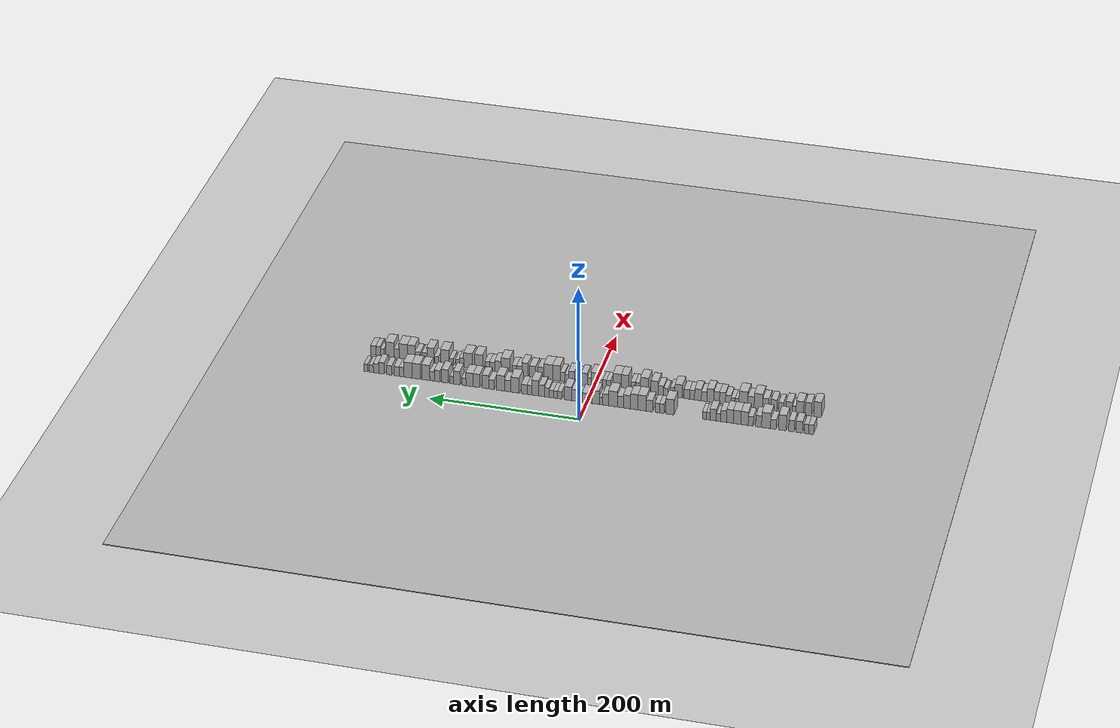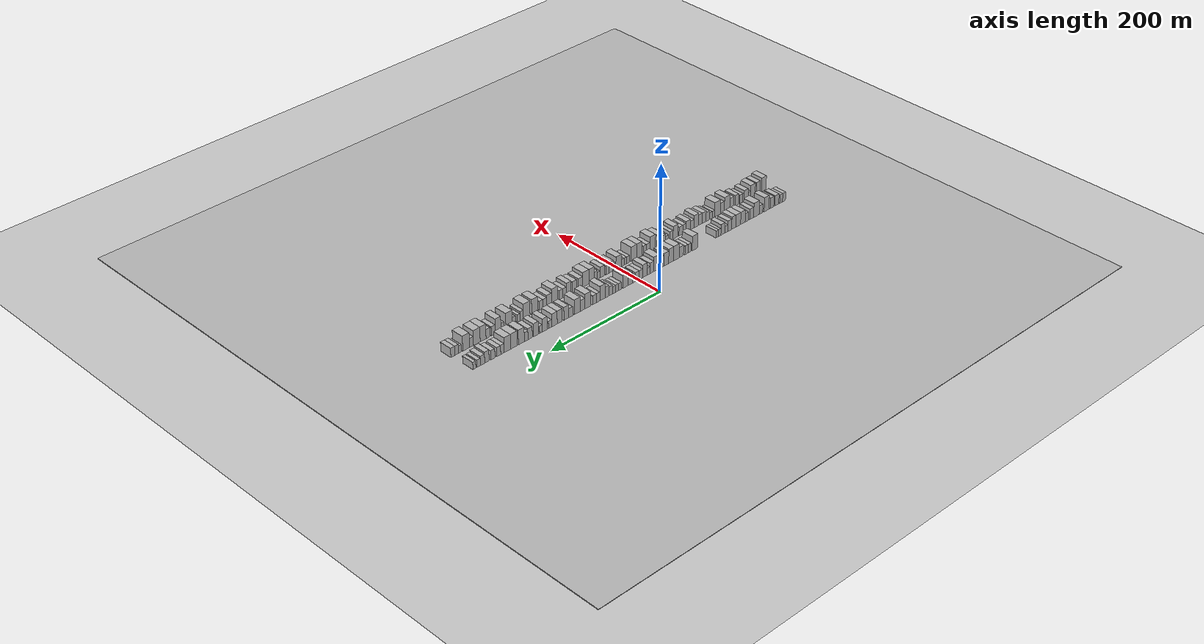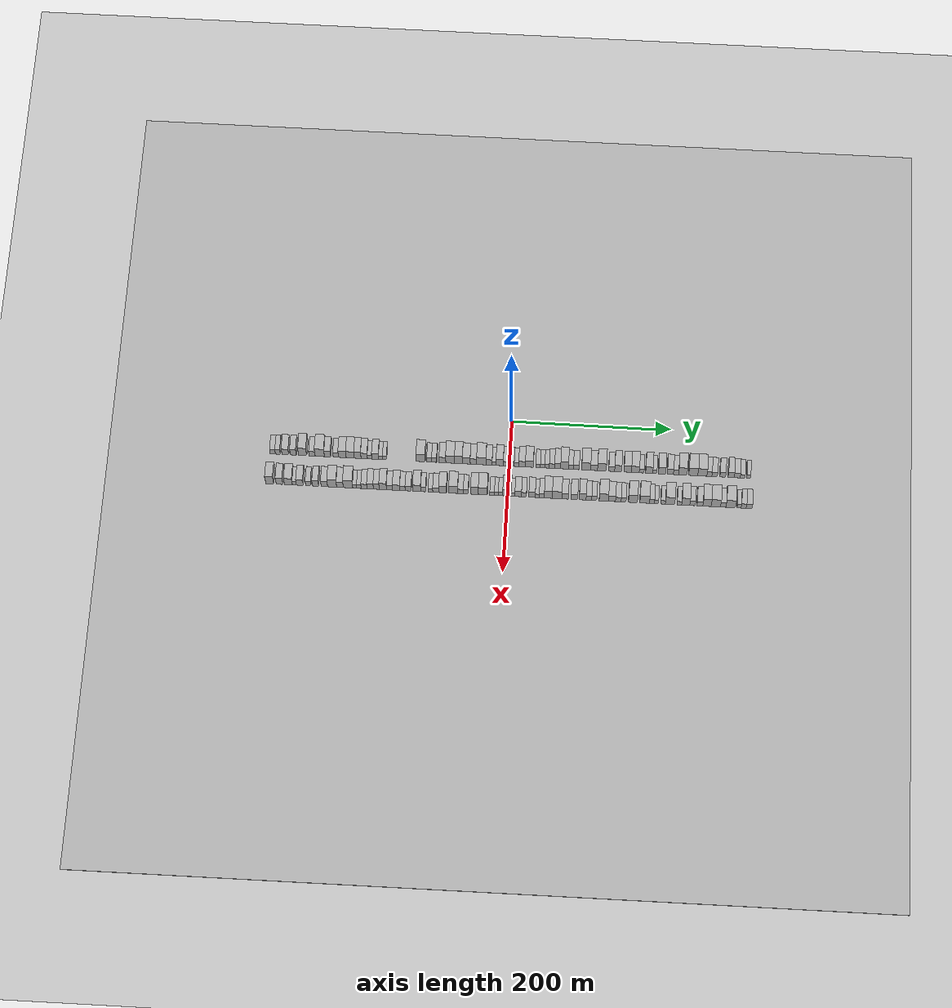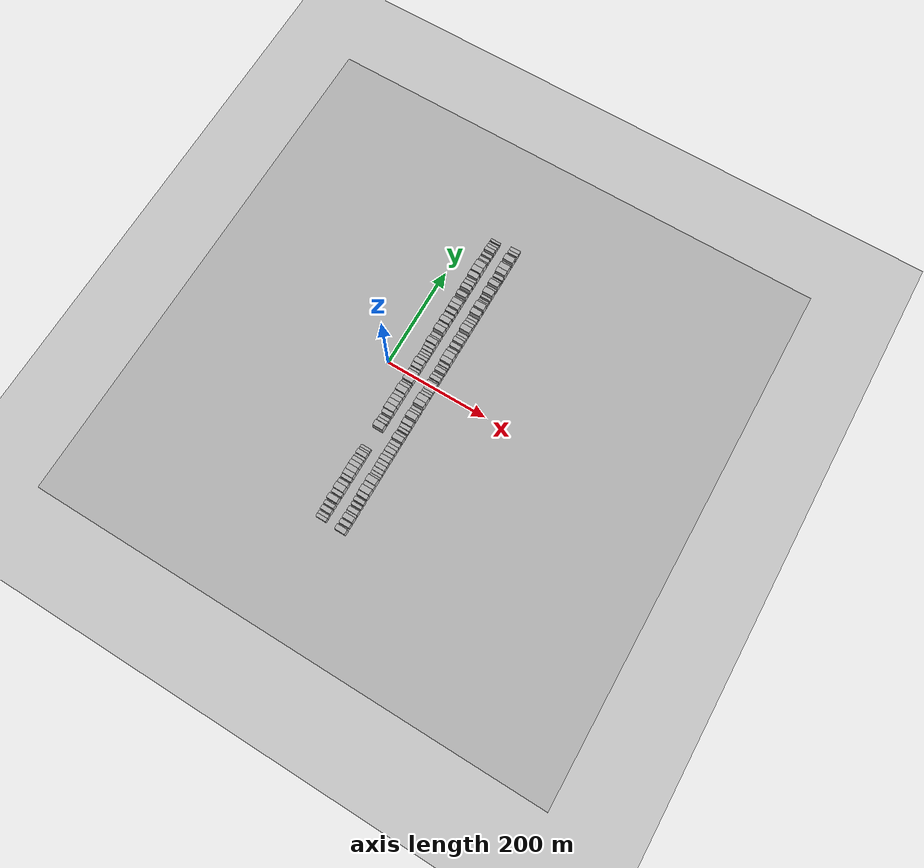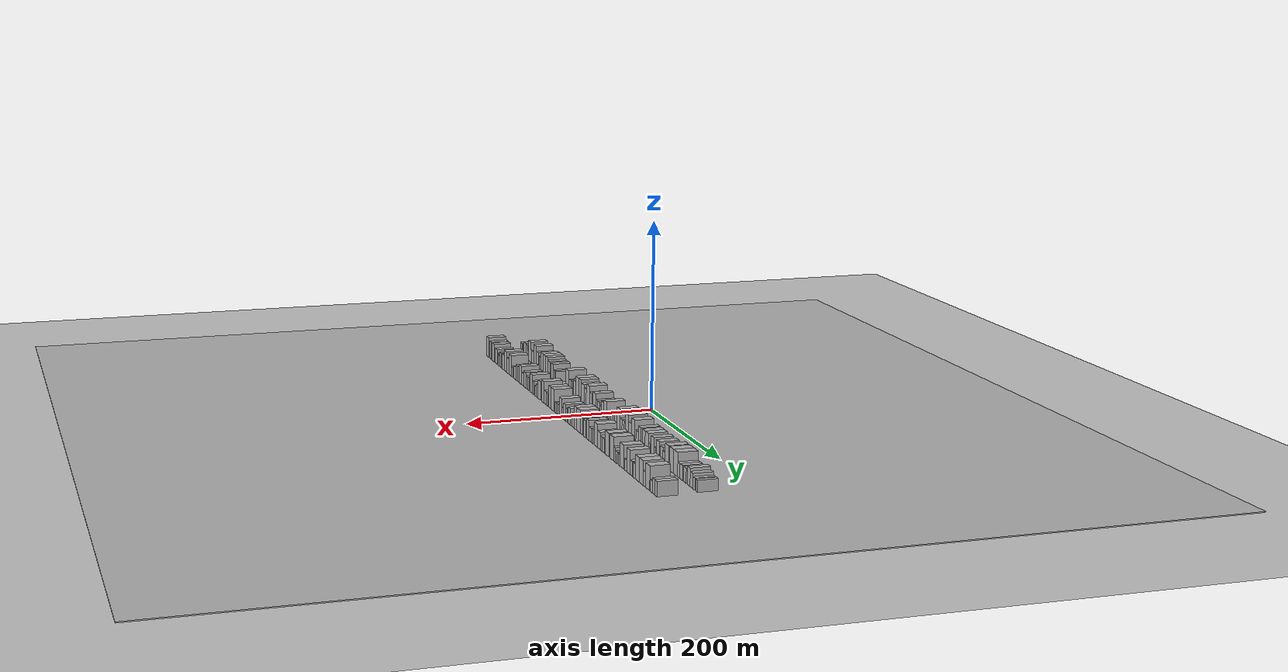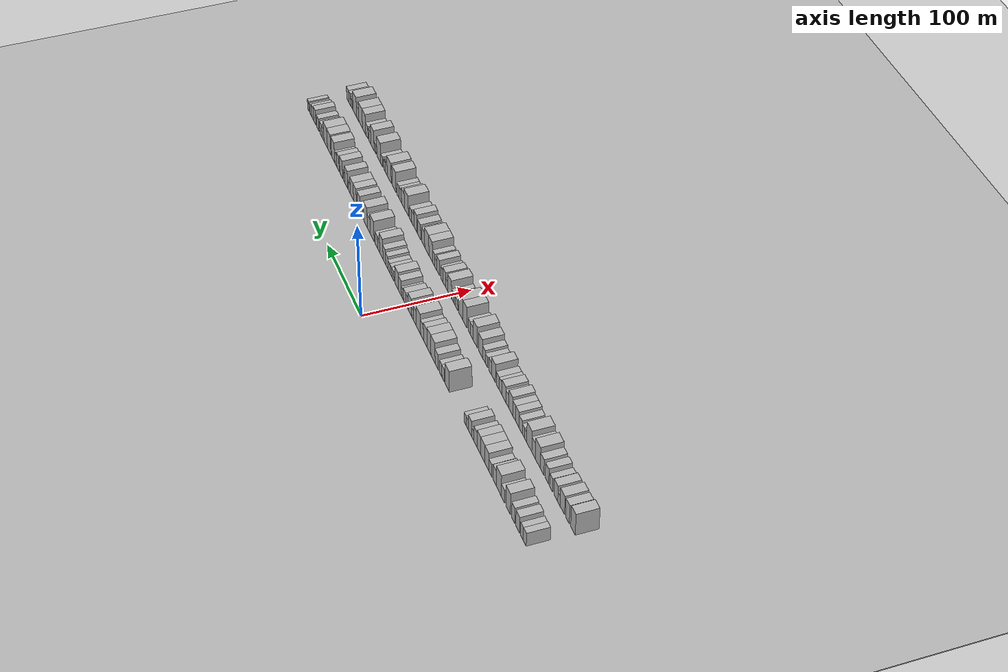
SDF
<?xml version="1.0" encoding="utf-8"?>

<sdf version="1.6">

   <world name="default">

      <gui fullscreen="0">

         <camera name="user_camera">

            <pose>-15 0 4.57585 0 0 0</pose>

            <view_controller>orbit</view_controller>

         </camera>

      </gui>

      <scene>

         <sky>

           <clouds>

             <speed>12</speed>

           </clouds>

         </sky>

         <ambient>0.4 0.4 0.4 1</ambient>

         <background>0.7 0.7 0.7 1</background>

         <shadows>1</shadows>

      </scene>

      <gravity>0 0 -9.8066</gravity>

      <magnetic_field>6e-06 2.3e-05 -4.2e-05</magnetic_field>

      <physics default="0" name="default_physics" type="ode">

         <ode>

            <solver>

               <type>quick</type>

               <iters>10</iters>

               <sor>1.0</sor>

               <use_dynamic_moi_rescaling>0</use_dynamic_moi_rescaling>

            </solver>

            <constraints>

               <cfm>0</cfm>

               <erp>0.2</erp>

               <contact_max_correcting_vel>100</contact_max_correcting_vel>

               <contact_surface_layer>0.001</contact_surface_layer>

            </constraints>

         </ode>

         <max_step_size>0.004</max_step_size>

         <real_time_factor>1</real_time_factor>

         <real_time_update_rate>250</real_time_update_rate>

      </physics>

      <light name="sun" type="directional">

         <cast_shadows>1</cast_shadows>

         <pose>0 0 10 0 0 0</pose>

         <diffuse>0.8 0.8 0.8 1</diffuse>

         <specular>0.2 0.2 0.2 1</specular>

         <attenuation>

            <range>1000</range>

            <constant>0.9</constant>

            <linear>0.01</linear>

            <quadratic>0.001</quadratic>

         </attenuation>

         <direction>-0.5 0.1 -0.9</direction>

      </light>

      <include>

         <name>ground_plane_1</name>

         <uri>model://HANNAS_ground_plane</uri>

         <pose>0 0 0  0 0 0</pose>

      </include>

      <include>

         <name>ground_plane_2</name>

         <uri>model://HANNAS_ground_plane</uri>

         <pose>100 0 0  0 0 0</pose>

      </include>

      <model name="building_1">

         <static>1</static>

         <pose frame="">50.0000 -294.6984 0 0.000000 0.000000 0.000000</pose>

         <link name="link">

            <pose frame="">0 0 7.50 0 0 0</pose>

            <collision name="collision">

               <geometry>

                  <box>

                     <size>20.0000 6.6032 15.0000</size>

                  </box>

               </geometry>

               <max_contacts>10</max_contacts>

               <surface>

                  <contact>

                     <ode/>

                  </contact>

                  <bounce/>

                  <friction>

                     <torsional>

                        <ode/>

                     </torsional>

                     <ode/>

                  </friction>

               </surface>

            </collision>

            <visual name="visual">

               <cast_shadows>0</cast_shadows>

               <geometry>

                  <box>

                     <size>20.0000 6.6032 15.0000</size>

                  </box>

               </geometry>

               <material>

                  <script>

                     <uri>model://HANNAS_wall/materials/scripts</uri>

                     <uri>model://HANNAS_wall/materials/textures</uri>

                     <name>vrc/HANNAS_wall</name>

                  </script>

               </material>

            </visual>

            <self_collide>0</self_collide>

            <enable_wind>0</enable_wind>

            <kinematic>0</kinematic>

         </link>

      </model>

      <model name="building_2">

         <static>1</static>

         <pose frame="">50.0000 -288.3703 0 0.000000 0.000000 0.000000</pose>

         <link name="link">

            <pose frame="">0 0 7.50 0 0 0</pose>

            <collision name="collision">

               <geometry>

                  <box>

                     <size>20.0000 6.0530 15.0000</size>

                  </box>

               </geometry>

               <max_contacts>10</max_contacts>

               <surface>

                  <contact>

                     <ode/>

                  </contact>

                  <bounce/>

                  <friction>

                     <torsional>

                        <ode/>

                     </torsional>

                     <ode/>

                  </friction>

               </surface>

            </collision>

            <visual name="visual">

               <cast_shadows>0</cast_shadows>

               <geometry>

                  <box>

                     <size>20.0000 6.0530 15.0000</size>

                  </box>

               </geometry>

               <material>

                  <script>

                     <uri>model://HANNAS_wall/materials/scripts</uri>

                     <uri>model://HANNAS_wall/materials/textures</uri>

                     <name>vrc/HANNAS_wall</name>

                  </script>

               </material>

            </visual>

            <self_collide>0</self_collide>

            <enable_wind>0</enable_wind>

            <kinematic>0</kinematic>

         </link>

      </model>

      <model name="building_3">

         <static>1</static>

         <pose frame="">50.0000 -279.0492 0 0.000000 0.000000 0.000000</pose>

         <link name="link">

            <pose frame="">0 0 9.00 0 0 0</pose>

            <collision name="collision">

               <geometry>

                  <box>

                     <size>20.0000 8.5891 18.0000</size>

                  </box>

               </geometry>

               <max_contacts>10</max_contacts>

               <surface>

                  <contact>

                     <ode/>

                  </contact>

                  <bounce/>

                  <friction>

                     <torsional>

                        <ode/>

                     </torsional>

                     <ode/>

                  </friction>

               </surface>

            </collision>

            <visual name="visual">

               <cast_shadows>0</cast_shadows>

               <geometry>

                  <box>

                     <size>20.0000 8.5891 18.0000</size>

                  </box>

               </geometry>

               <material>

                  <script>

                     <uri>model://HANNAS_wall/materials/scripts</uri>

                     <uri>model://HANNAS_wall/materials/textures</uri>

                     <name>vrc/HANNAS_wall</name>

                  </script>

               </material>

            </visual>

            <self_collide>0</self_collide>

            <enable_wind>0</enable_wind>

            <kinematic>0</kinematic>

         </link>

      </model>

      <model name="building_4">

         <static>1</static>

         <pose frame="">50.0000 -269.0893 0 0.000000 0.000000 0.000000</pose>

         <link name="link">

            <pose frame="">0 0 9.00 0 0 0</pose>

            <collision name="collision">

               <geometry>

                  <box>

                     <size>20.0000 7.3307 18.0000</size>

                  </box>

               </geometry>

               <max_contacts>10</max_contacts>

               <surface>

                  <contact>

                     <ode/>

                  </contact>

                  <bounce/>

                  <friction>

                     <torsional>

                        <ode/>

                     </torsional>

                     <ode/>

                  </friction>

               </surface>

            </collision>

            <visual name="visual">

               <cast_shadows>0</cast_shadows>

               <geometry>

                  <box>

                     <size>20.0000 7.3307 18.0000</size>

                  </box>

               </geometry>

               <material>

                  <script>

                     <uri>model://HANNAS_wall/materials/scripts</uri>

                     <uri>model://HANNAS_wall/materials/textures</uri>

                     <name>vrc/HANNAS_wall</name>

                  </script>

               </material>

            </visual>

            <self_collide>0</self_collide>

            <enable_wind>0</enable_wind>

            <kinematic>0</kinematic>

         </link>

      </model>

      <model name="building_5">

         <static>1</static>

         <pose frame="">50.0000 -257.3650 0 0.000000 0.000000 0.000000</pose>

         <link name="link">

            <pose frame="">0 0 12.00 0 0 0</pose>

            <collision name="collision">

               <geometry>

                  <box>

                     <size>20.0000 10.1179 24.0000</size>

                  </box>

               </geometry>

               <max_contacts>10</max_contacts>

               <surface>

                  <contact>

                     <ode/>

                  </contact>

                  <bounce/>

                  <friction>

                     <torsional>

                        <ode/>

                     </torsional>

                     <ode/>

                  </friction>

               </surface>

            </collision>

            <visual name="visual">

               <cast_shadows>0</cast_shadows>

               <geometry>

                  <box>

                     <size>20.0000 10.1179 24.0000</size>

                  </box>

               </geometry>

               <material>

                  <script>

                     <uri>model://HANNAS_wall/materials/scripts</uri>

                     <uri>model://HANNAS_wall/materials/textures</uri>

                     <name>vrc/HANNAS_wall</name>

                  </script>

               </material>

            </visual>

            <self_collide>0</self_collide>

            <enable_wind>0</enable_wind>

            <kinematic>0</kinematic>

         </link>

      </model>

      <model name="building_6">

         <static>1</static>

         <pose frame="">50.0000 -245.5570 0 0.000000 0.000000 0.000000</pose>

         <link name="link">

            <pose frame="">0 0 7.50 0 0 0</pose>

            <collision name="collision">

               <geometry>

                  <box>

                     <size>20.0000 7.4982 15.0000</size>

                  </box>

               </geometry>

               <max_contacts>10</max_contacts>

               <surface>

                  <contact>

                     <ode/>

                  </contact>

                  <bounce/>

                  <friction>

                     <torsional>

                        <ode/>

                     </torsional>

                     <ode/>

                  </friction>

               </surface>

            </collision>

            <visual name="visual">

               <cast_shadows>0</cast_shadows>

               <geometry>

                  <box>

                     <size>20.0000 7.4982 15.0000</size>

                  </box>

               </geometry>

               <material>

                  <script>

                     <uri>model://HANNAS_wall/materials/scripts</uri>

                     <uri>model://HANNAS_wall/materials/textures</uri>

                     <name>vrc/HANNAS_wall</name>

                  </script>

               </material>

            </visual>

            <self_collide>0</self_collide>

            <enable_wind>0</enable_wind>

            <kinematic>0</kinematic>

         </link>

      </model>

      <model name="building_7">

         <static>1</static>

         <pose frame="">50.0000 -235.9556 0 0.000000 0.000000 0.000000</pose>

         <link name="link">

            <pose frame="">0 0 12.00 0 0 0</pose>

            <collision name="collision">

               <geometry>

                  <box>

                     <size>20.0000 11.7046 24.0000</size>

                  </box>

               </geometry>

               <max_contacts>10</max_contacts>

               <surface>

                  <contact>

                     <ode/>

                  </contact>

                  <bounce/>

                  <friction>

                     <torsional>

                        <ode/>

                     </torsional>

                     <ode/>

                  </friction>

               </surface>

            </collision>

            <visual name="visual">

               <cast_shadows>0</cast_shadows>

               <geometry>

                  <box>

                     <size>20.0000 11.7046 24.0000</size>

                  </box>

               </geometry>

               <material>

                  <script>

                     <uri>model://HANNAS_wall/materials/scripts</uri>

                     <uri>model://HANNAS_wall/materials/textures</uri>

                     <name>vrc/HANNAS_wall</name>

                  </script>

               </material>

            </visual>

            <self_collide>0</self_collide>

            <enable_wind>0</enable_wind>

            <kinematic>0</kinematic>

         </link>

      </model>

      <model name="building_8">

         <static>1</static>

         <pose frame="">50.0000 -226.2014 0 0.000000 0.000000 0.000000</pose>

         <link name="link">

            <pose frame="">0 0 9.00 0 0 0</pose>

            <collision name="collision">

               <geometry>

                  <box>

                     <size>20.0000 7.8038 18.0000</size>

                  </box>

               </geometry>

               <max_contacts>10</max_contacts>

               <surface>

                  <contact>

                     <ode/>

                  </contact>

                  <bounce/>

                  <friction>

                     <torsional>

                        <ode/>

                     </torsional>

                     <ode/>

                  </friction>

               </surface>

            </collision>

            <visual name="visual">

               <cast_shadows>0</cast_shadows>

               <geometry>

                  <box>

                     <size>20.0000 7.8038 18.0000</size>

                  </box>

               </geometry>

               <material>

                  <script>

                     <uri>model://HANNAS_wall/materials/scripts</uri>

                     <uri>model://HANNAS_wall/materials/textures</uri>

                     <name>vrc/HANNAS_wall</name>

                  </script>

               </material>

            </visual>

            <self_collide>0</self_collide>

            <enable_wind>0</enable_wind>

            <kinematic>0</kinematic>

         </link>

      </model>

      <model name="building_9">

         <static>1</static>

         <pose frame="">50.0000 -215.9153 0 0.000000 0.000000 0.000000</pose>

         <link name="link">

            <pose frame="">0 0 7.50 0 0 0</pose>

            <collision name="collision">

               <geometry>

                  <box>

                     <size>20.0000 6.7684 15.0000</size>

                  </box>

               </geometry>

               <max_contacts>10</max_contacts>

               <surface>

                  <contact>

                     <ode/>

                  </contact>

                  <bounce/>

                  <friction>

                     <torsional>

                        <ode/>

                     </torsional>

                     <ode/>

                  </friction>

               </surface>

            </collision>

            <visual name="visual">

               <cast_shadows>0</cast_shadows>

               <geometry>

                  <box>

                     <size>20.0000 6.7684 15.0000</size>

                  </box>

               </geometry>

               <material>

                  <script>

                     <uri>model://HANNAS_wall/materials/scripts</uri>

                     <uri>model://HANNAS_wall/materials/textures</uri>

                     <name>vrc/HANNAS_wall</name>

                  </script>

               </material>

            </visual>

            <self_collide>0</self_collide>

            <enable_wind>0</enable_wind>

            <kinematic>0</kinematic>

         </link>

      </model>

      <model name="building_10">

         <static>1</static>

         <pose frame="">50.0000 -207.8141 0 0.000000 0.000000 0.000000</pose>

         <link name="link">

            <pose frame="">0 0 10.50 0 0 0</pose>

            <collision name="collision">

               <geometry>

                  <box>

                     <size>20.0000 9.4342 21.0000</size>

                  </box>

               </geometry>

               <max_contacts>10</max_contacts>

               <surface>

                  <contact>

                     <ode/>

                  </contact>

                  <bounce/>

                  <friction>

                     <torsional>

                        <ode/>

                     </torsional>

                     <ode/>

                  </friction>

               </surface>

            </collision>

            <visual name="visual">

               <cast_shadows>0</cast_shadows>

               <geometry>

                  <box>

                     <size>20.0000 9.4342 21.0000</size>

                  </box>

               </geometry>

               <material>

                  <script>

                     <uri>model://HANNAS_wall/materials/scripts</uri>

                     <uri>model://HANNAS_wall/materials/textures</uri>

                     <name>vrc/HANNAS_wall</name>

                  </script>

               </material>

            </visual>

            <self_collide>0</self_collide>

            <enable_wind>0</enable_wind>

            <kinematic>0</kinematic>

         </link>

      </model>

      <model name="building_11">

         <static>1</static>

         <pose frame="">50.0000 -197.9994 0 0.000000 0.000000 0.000000</pose>

         <link name="link">

            <pose frame="">0 0 10.50 0 0 0</pose>

            <collision name="collision">

               <geometry>

                  <box>

                     <size>20.0000 10.1951 21.0000</size>

                  </box>

               </geometry>

               <max_contacts>10</max_contacts>

               <surface>

                  <contact>

                     <ode/>

                  </contact>

                  <bounce/>

                  <friction>

                     <torsional>

                        <ode/>

                     </torsional>

                     <ode/>

                  </friction>

               </surface>

            </collision>

            <visual name="visual">

               <cast_shadows>0</cast_shadows>

               <geometry>

                  <box>

                     <size>20.0000 10.1951 21.0000</size>

                  </box>

               </geometry>

               <material>

                  <script>

                     <uri>model://HANNAS_wall/materials/scripts</uri>

                     <uri>model://HANNAS_wall/materials/textures</uri>

                     <name>vrc/HANNAS_wall</name>

                  </script>

               </material>

            </visual>

            <self_collide>0</self_collide>

            <enable_wind>0</enable_wind>

            <kinematic>0</kinematic>

         </link>

      </model>

      <model name="building_12">

         <static>1</static>

         <pose frame="">50.0000 -188.6999 0 0.000000 0.000000 0.000000</pose>

         <link name="link">

            <pose frame="">0 0 10.50 0 0 0</pose>

            <collision name="collision">

               <geometry>

                  <box>

                     <size>20.0000 8.4037 21.0000</size>

                  </box>

               </geometry>

               <max_contacts>10</max_contacts>

               <surface>

                  <contact>

                     <ode/>

                  </contact>

                  <bounce/>

                  <friction>

                     <torsional>

                        <ode/>

                     </torsional>

                     <ode/>

                  </friction>

               </surface>

            </collision>

            <visual name="visual">

               <cast_shadows>0</cast_shadows>

               <geometry>

                  <box>

                     <size>20.0000 8.4037 21.0000</size>

                  </box>

               </geometry>

               <material>

                  <script>

                     <uri>model://HANNAS_wall/materials/scripts</uri>

                     <uri>model://HANNAS_wall/materials/textures</uri>

                     <name>vrc/HANNAS_wall</name>

                  </script>

               </material>

            </visual>

            <self_collide>0</self_collide>

            <enable_wind>0</enable_wind>

            <kinematic>0</kinematic>

         </link>

      </model>

      <model name="building_13">

         <static>1</static>

         <pose frame="">50.0000 -180.5079 0 0.000000 0.000000 0.000000</pose>

         <link name="link">

            <pose frame="">0 0 9.00 0 0 0</pose>

            <collision name="collision">

               <geometry>

                  <box>

                     <size>20.0000 7.9804 18.0000</size>

                  </box>

               </geometry>

               <max_contacts>10</max_contacts>

               <surface>

                  <contact>

                     <ode/>

                  </contact>

                  <bounce/>

                  <friction>

                     <torsional>

                        <ode/>

                     </torsional>

                     <ode/>

                  </friction>

               </surface>

            </collision>

            <visual name="visual">

               <cast_shadows>0</cast_shadows>

               <geometry>

                  <box>

                     <size>20.0000 7.9804 18.0000</size>

                  </box>

               </geometry>

               <material>

                  <script>

                     <uri>model://HANNAS_wall/materials/scripts</uri>

                     <uri>model://HANNAS_wall/materials/textures</uri>

                     <name>vrc/HANNAS_wall</name>

                  </script>

               </material>

            </visual>

            <self_collide>0</self_collide>

            <enable_wind>0</enable_wind>

            <kinematic>0</kinematic>

         </link>

      </model>

      <model name="building_14">

         <static>1</static>

         <pose frame="">50.0000 -173.7008 0 0.000000 0.000000 0.000000</pose>

         <link name="link">

            <pose frame="">0 0 6.00 0 0 0</pose>

            <collision name="collision">

               <geometry>

                  <box>

                     <size>20.0000 5.6337 12.0000</size>

                  </box>

               </geometry>

               <max_contacts>10</max_contacts>

               <surface>

                  <contact>

                     <ode/>

                  </contact>

                  <bounce/>

                  <friction>

                     <torsional>

                        <ode/>

                     </torsional>

                     <ode/>

                  </friction>

               </surface>

            </collision>

            <visual name="visual">

               <cast_shadows>0</cast_shadows>

               <geometry>

                  <box>

                     <size>20.0000 5.6337 12.0000</size>

                  </box>

               </geometry>

               <material>

                  <script>

                     <uri>model://HANNAS_wall/materials/scripts</uri>

                     <uri>model://HANNAS_wall/materials/textures</uri>

                     <name>vrc/HANNAS_wall</name>

                  </script>

               </material>

            </visual>

            <self_collide>0</self_collide>

            <enable_wind>0</enable_wind>

            <kinematic>0</kinematic>

         </link>

      </model>

      <model name="building_15">

         <static>1</static>

         <pose frame="">50.0000 -166.6920 0 0.000000 0.000000 0.000000</pose>

         <link name="link">

            <pose frame="">0 0 9.00 0 0 0</pose>

            <collision name="collision">

               <geometry>

                  <box>

                     <size>20.0000 8.3840 18.0000</size>

                  </box>

               </geometry>

               <max_contacts>10</max_contacts>

               <surface>

                  <contact>

                     <ode/>

                  </contact>

                  <bounce/>

                  <friction>

                     <torsional>

                        <ode/>

                     </torsional>

                     <ode/>

                  </friction>

               </surface>

            </collision>

            <visual name="visual">

               <cast_shadows>0</cast_shadows>

               <geometry>

                  <box>

                     <size>20.0000 8.3840 18.0000</size>

                  </box>

               </geometry>

               <material>

                  <script>

                     <uri>model://HANNAS_wall/materials/scripts</uri>

                     <uri>model://HANNAS_wall/materials/textures</uri>

                     <name>vrc/HANNAS_wall</name>

                  </script>

               </material>

            </visual>

            <self_collide>0</self_collide>

            <enable_wind>0</enable_wind>

            <kinematic>0</kinematic>

         </link>

      </model>

      <model name="building_16">

         <static>1</static>

         <pose frame="">50.0000 -160.0304 0 0.000000 0.000000 0.000000</pose>

         <link name="link">

            <pose frame="">0 0 6.00 0 0 0</pose>

            <collision name="collision">

               <geometry>

                  <box>

                     <size>20.0000 4.9392 12.0000</size>

                  </box>

               </geometry>

               <max_contacts>10</max_contacts>

               <surface>

                  <contact>

                     <ode/>

                  </contact>

                  <bounce/>

                  <friction>

                     <torsional>

                        <ode/>

                     </torsional>

                     <ode/>

                  </friction>

               </surface>

            </collision>

            <visual name="visual">

               <cast_shadows>0</cast_shadows>

               <geometry>

                  <box>

                     <size>20.0000 4.9392 12.0000</size>

                  </box>

               </geometry>

               <material>

                  <script>

                     <uri>model://HANNAS_wall/materials/scripts</uri>

                     <uri>model://HANNAS_wall/materials/textures</uri>

                     <name>vrc/HANNAS_wall</name>

                  </script>

               </material>

            </visual>

            <self_collide>0</self_collide>

            <enable_wind>0</enable_wind>

            <kinematic>0</kinematic>

         </link>

      </model>

      <model name="building_17">

         <static>1</static>

         <pose frame="">50.0000 -155.0793 0 0.000000 0.000000 0.000000</pose>

         <link name="link">

            <pose frame="">0 0 6.00 0 0 0</pose>

            <collision name="collision">

               <geometry>

                  <box>

                     <size>20.0000 4.9629 12.0000</size>

                  </box>

               </geometry>

               <max_contacts>10</max_contacts>

               <surface>

                  <contact>

                     <ode/>

                  </contact>

                  <bounce/>

                  <friction>

                     <torsional>

                        <ode/>

                     </torsional>

                     <ode/>

                  </friction>

               </surface>

            </collision>

            <visual name="visual">

               <cast_shadows>0</cast_shadows>

               <geometry>

                  <box>

                     <size>20.0000 4.9629 12.0000</size>

                  </box>

               </geometry>

               <material>

                  <script>

                     <uri>model://HANNAS_wall/materials/scripts</uri>

                     <uri>model://HANNAS_wall/materials/textures</uri>

                     <name>vrc/HANNAS_wall</name>

                  </script>

               </material>

            </visual>

            <self_collide>0</self_collide>

            <enable_wind>0</enable_wind>

            <kinematic>0</kinematic>

         </link>

      </model>

      <model name="building_18">

         <static>1</static>

         <pose frame="">50.0000 -109.8939 0 0.000000 0.000000 0.000000</pose>

         <link name="link">

            <pose frame="">0 0 12.00 0 0 0</pose>

            <collision name="collision">

               <geometry>

                  <box>

                     <size>20.0000 11.1360 24.0000</size>

                  </box>

               </geometry>

               <max_contacts>10</max_contacts>

               <surface>

                  <contact>

                     <ode/>

                  </contact>

                  <bounce/>

                  <friction>

                     <torsional>

                        <ode/>

                     </torsional>

                     <ode/>

                  </friction>

               </surface>

            </collision>

            <visual name="visual">

               <cast_shadows>0</cast_shadows>

               <geometry>

                  <box>

                     <size>20.0000 11.1360 24.0000</size>

                  </box>

               </geometry>

               <material>

                  <script>

                     <uri>model://HANNAS_wall/materials/scripts</uri>

                     <uri>model://HANNAS_wall/materials/textures</uri>

                     <name>vrc/HANNAS_wall</name>

                  </script>

               </material>

            </visual>

            <self_collide>0</self_collide>

            <enable_wind>0</enable_wind>

            <kinematic>0</kinematic>

         </link>

      </model>

      <model name="building_19">

         <static>1</static>

         <pose frame="">50.0000 -99.2927 0 0.000000 0.000000 0.000000</pose>

         <link name="link">

            <pose frame="">0 0 7.50 0 0 0</pose>

            <collision name="collision">

               <geometry>

                  <box>

                     <size>20.0000 6.0665 15.0000</size>

                  </box>

               </geometry>

               <max_contacts>10</max_contacts>

               <surface>

                  <contact>

                     <ode/>

                  </contact>

                  <bounce/>

                  <friction>

                     <torsional>

                        <ode/>

                     </torsional>

                     <ode/>

                  </friction>

               </surface>

            </collision>

            <visual name="visual">

               <cast_shadows>0</cast_shadows>

               <geometry>

                  <box>

                     <size>20.0000 6.0665 15.0000</size>

                  </box>

               </geometry>

               <material>

                  <script>

                     <uri>model://HANNAS_wall/materials/scripts</uri>

                     <uri>model://HANNAS_wall/materials/textures</uri>

                     <name>vrc/HANNAS_wall</name>

                  </script>

               </material>

            </visual>

            <self_collide>0</self_collide>

            <enable_wind>0</enable_wind>

            <kinematic>0</kinematic>

         </link>

      </model>

      <model name="building_20">

         <static>1</static>

         <pose frame="">50.0000 -93.1286 0 0.000000 0.000000 0.000000</pose>

         <link name="link">

            <pose frame="">0 0 7.50 0 0 0</pose>

            <collision name="collision">

               <geometry>

                  <box>

                     <size>20.0000 6.2618 15.0000</size>

                  </box>

               </geometry>

               <max_contacts>10</max_contacts>

               <surface>

                  <contact>

                     <ode/>

                  </contact>

                  <bounce/>

                  <friction>

                     <torsional>

                        <ode/>

                     </torsional>

                     <ode/>

                  </friction>

               </surface>

            </collision>

            <visual name="visual">

               <cast_shadows>0</cast_shadows>

               <geometry>

                  <box>

                     <size>20.0000 6.2618 15.0000</size>

                  </box>

               </geometry>

               <material>

                  <script>

                     <uri>model://HANNAS_wall/materials/scripts</uri>

                     <uri>model://HANNAS_wall/materials/textures</uri>

                     <name>vrc/HANNAS_wall</name>

                  </script>

               </material>

            </visual>

            <self_collide>0</self_collide>

            <enable_wind>0</enable_wind>

            <kinematic>0</kinematic>

         </link>

      </model>

      <model name="building_21">

         <static>1</static>

         <pose frame="">50.0000 -82.8432 0 0.000000 0.000000 0.000000</pose>

         <link name="link">

            <pose frame="">0 0 9.00 0 0 0</pose>

            <collision name="collision">

               <geometry>

                  <box>

                     <size>20.0000 8.3088 18.0000</size>

                  </box>

               </geometry>

               <max_contacts>10</max_contacts>

               <surface>

                  <contact>

                     <ode/>

                  </contact>

                  <bounce/>

                  <friction>

                     <torsional>

                        <ode/>

                     </torsional>

                     <ode/>

                  </friction>

               </surface>

            </collision>

            <visual name="visual">

               <cast_shadows>0</cast_shadows>

               <geometry>

                  <box>

                     <size>20.0000 8.3088 18.0000</size>

                  </box>

               </geometry>

               <material>

                  <script>

                     <uri>model://HANNAS_wall/materials/scripts</uri>

                     <uri>model://HANNAS_wall/materials/textures</uri>

                     <name>vrc/HANNAS_wall</name>

                  </script>

               </material>

            </visual>

            <self_collide>0</self_collide>

            <enable_wind>0</enable_wind>

            <kinematic>0</kinematic>

         </link>

      </model>

      <model name="building_22">

         <static>1</static>

         <pose frame="">50.0000 -73.1560 0 0.000000 0.000000 0.000000</pose>

         <link name="link">

            <pose frame="">0 0 12.00 0 0 0</pose>

            <collision name="collision">

               <geometry>

                  <box>

                     <size>20.0000 11.0657 24.0000</size>

                  </box>

               </geometry>

               <max_contacts>10</max_contacts>

               <surface>

                  <contact>

                     <ode/>

                  </contact>

                  <bounce/>

                  <friction>

                     <torsional>

                        <ode/>

                     </torsional>

                     <ode/>

                  </friction>

               </surface>

            </collision>

            <visual name="visual">

               <cast_shadows>0</cast_shadows>

               <geometry>

                  <box>

                     <size>20.0000 11.0657 24.0000</size>

                  </box>

               </geometry>

               <material>

                  <script>

                     <uri>model://HANNAS_wall/materials/scripts</uri>

                     <uri>model://HANNAS_wall/materials/textures</uri>

                     <name>vrc/HANNAS_wall</name>

                  </script>

               </material>

            </visual>

            <self_collide>0</self_collide>

            <enable_wind>0</enable_wind>

            <kinematic>0</kinematic>

         </link>

      </model>

      <model name="building_23">

         <static>1</static>

         <pose frame="">50.0000 -62.7420 0 0.000000 0.000000 0.000000</pose>

         <link name="link">

            <pose frame="">0 0 12.00 0 0 0</pose>

            <collision name="collision">

               <geometry>

                  <box>

                     <size>20.0000 9.7621 24.0000</size>

                  </box>

               </geometry>

               <max_contacts>10</max_contacts>

               <surface>

                  <contact>

                     <ode/>

                  </contact>

                  <bounce/>

                  <friction>

                     <torsional>

                        <ode/>

                     </torsional>

                     <ode/>

                  </friction>

               </surface>

            </collision>

            <visual name="visual">

               <cast_shadows>0</cast_shadows>

               <geometry>

                  <box>

                     <size>20.0000 9.7621 24.0000</size>

                  </box>

               </geometry>

               <material>

                  <script>

                     <uri>model://HANNAS_wall/materials/scripts</uri>

                     <uri>model://HANNAS_wall/materials/textures</uri>

                     <name>vrc/HANNAS_wall</name>

                  </script>

               </material>

            </visual>

            <self_collide>0</self_collide>

            <enable_wind>0</enable_wind>

            <kinematic>0</kinematic>

         </link>

      </model>

      <model name="building_24">

         <static>1</static>

         <pose frame="">50.0000 -53.0204 0 0.000000 0.000000 0.000000</pose>

         <link name="link">

            <pose frame="">0 0 10.50 0 0 0</pose>

            <collision name="collision">

               <geometry>

                  <box>

                     <size>20.0000 9.6811 21.0000</size>

                  </box>

               </geometry>

               <max_contacts>10</max_contacts>

               <surface>

                  <contact>

                     <ode/>

                  </contact>

                  <bounce/>

                  <friction>

                     <torsional>

                        <ode/>

                     </torsional>

                     <ode/>

                  </friction>

               </surface>

            </collision>

            <visual name="visual">

               <cast_shadows>0</cast_shadows>

               <geometry>

                  <box>

                     <size>20.0000 9.6811 21.0000</size>

                  </box>

               </geometry>

               <material>

                  <script>

                     <uri>model://HANNAS_wall/materials/scripts</uri>

                     <uri>model://HANNAS_wall/materials/textures</uri>

                     <name>vrc/HANNAS_wall</name>

                  </script>

               </material>

            </visual>

            <self_collide>0</self_collide>

            <enable_wind>0</enable_wind>

            <kinematic>0</kinematic>

         </link>

      </model>

      <model name="building_25">

         <static>1</static>

         <pose frame="">50.0000 -44.1739 0 0.000000 0.000000 0.000000</pose>

         <link name="link">

            <pose frame="">0 0 9.00 0 0 0</pose>

            <collision name="collision">

               <geometry>

                  <box>

                     <size>20.0000 8.0121 18.0000</size>

                  </box>

               </geometry>

               <max_contacts>10</max_contacts>

               <surface>

                  <contact>

                     <ode/>

                  </contact>

                  <bounce/>

                  <friction>

                     <torsional>

                        <ode/>

                     </torsional>

                     <ode/>

                  </friction>

               </surface>

            </collision>

            <visual name="visual">

               <cast_shadows>0</cast_shadows>

               <geometry>

                  <box>

                     <size>20.0000 8.0121 18.0000</size>

                  </box>

               </geometry>

               <material>

                  <script>

                     <uri>model://HANNAS_wall/materials/scripts</uri>

                     <uri>model://HANNAS_wall/materials/textures</uri>

                     <name>vrc/HANNAS_wall</name>

                  </script>

               </material>

            </visual>

            <self_collide>0</self_collide>

            <enable_wind>0</enable_wind>

            <kinematic>0</kinematic>

         </link>

      </model>

      <model name="building_26">

         <static>1</static>

         <pose frame="">50.0000 -34.3919 0 0.000000 0.000000 0.000000</pose>

         <link name="link">

            <pose frame="">0 0 12.00 0 0 0</pose>

            <collision name="collision">

               <geometry>

                  <box>

                     <size>20.0000 11.5519 24.0000</size>

                  </box>

               </geometry>

               <max_contacts>10</max_contacts>

               <surface>

                  <contact>

                     <ode/>

                  </contact>

                  <bounce/>

                  <friction>

                     <torsional>

                        <ode/>

                     </torsional>

                     <ode/>

                  </friction>

               </surface>

            </collision>

            <visual name="visual">

               <cast_shadows>0</cast_shadows>

               <geometry>

                  <box>

                     <size>20.0000 11.5519 24.0000</size>

                  </box>

               </geometry>

               <material>

                  <script>

                     <uri>model://HANNAS_wall/materials/scripts</uri>

                     <uri>model://HANNAS_wall/materials/textures</uri>

                     <name>vrc/HANNAS_wall</name>

                  </script>

               </material>

            </visual>

            <self_collide>0</self_collide>

            <enable_wind>0</enable_wind>

            <kinematic>0</kinematic>

         </link>

      </model>

      <model name="building_27">

         <static>1</static>

         <pose frame="">50.0000 -24.7512 0 0.000000 0.000000 0.000000</pose>

         <link name="link">

            <pose frame="">0 0 9.00 0 0 0</pose>

            <collision name="collision">

               <geometry>

                  <box>

                     <size>20.0000 7.7294 18.0000</size>

                  </box>

               </geometry>

               <max_contacts>10</max_contacts>

               <surface>

                  <contact>

                     <ode/>

                  </contact>

                  <bounce/>

                  <friction>

                     <torsional>

                        <ode/>

                     </torsional>

                     <ode/>

                  </friction>

               </surface>

            </collision>

            <visual name="visual">

               <cast_shadows>0</cast_shadows>

               <geometry>

                  <box>

                     <size>20.0000 7.7294 18.0000</size>

                  </box>

               </geometry>

               <material>

                  <script>

                     <uri>model://HANNAS_wall/materials/scripts</uri>

                     <uri>model://HANNAS_wall/materials/textures</uri>

                     <name>vrc/HANNAS_wall</name>

                  </script>

               </material>

            </visual>

            <self_collide>0</self_collide>

            <enable_wind>0</enable_wind>

            <kinematic>0</kinematic>

         </link>

      </model>

      <model name="building_28">

         <static>1</static>

         <pose frame="">50.0000 -18.4788 0 0.000000 0.000000 0.000000</pose>

         <link name="link">

            <pose frame="">0 0 6.00 0 0 0</pose>

            <collision name="collision">

               <geometry>

                  <box>

                     <size>20.0000 4.8155 12.0000</size>

                  </box>

               </geometry>

               <max_contacts>10</max_contacts>

               <surface>

                  <contact>

                     <ode/>

                  </contact>

                  <bounce/>

                  <friction>

                     <torsional>

                        <ode/>

                     </torsional>

                     <ode/>

                  </friction>

               </surface>

            </collision>

            <visual name="visual">

               <cast_shadows>0</cast_shadows>

               <geometry>

                  <box>

                     <size>20.0000 4.8155 12.0000</size>

                  </box>

               </geometry>

               <material>

                  <script>

                     <uri>model://HANNAS_wall/materials/scripts</uri>

                     <uri>model://HANNAS_wall/materials/textures</uri>

                     <name>vrc/HANNAS_wall</name>

                  </script>

               </material>

            </visual>

            <self_collide>0</self_collide>

            <enable_wind>0</enable_wind>

            <kinematic>0</kinematic>

         </link>

      </model>

      <model name="building_29">

         <static>1</static>

         <pose frame="">50.0000 -11.5415 0 0.000000 0.000000 0.000000</pose>

         <link name="link">

            <pose frame="">0 0 10.50 0 0 0</pose>

            <collision name="collision">

               <geometry>

                  <box>

                     <size>20.0000 9.0590 21.0000</size>

                  </box>

               </geometry>

               <max_contacts>10</max_contacts>

               <surface>

                  <contact>

                     <ode/>

                  </contact>

                  <bounce/>

                  <friction>

                     <torsional>

                        <ode/>

                     </torsional>

                     <ode/>

                  </friction>

               </surface>

            </collision>

            <visual name="visual">

               <cast_shadows>0</cast_shadows>

               <geometry>

                  <box>

                     <size>20.0000 9.0590 21.0000</size>

                  </box>

               </geometry>

               <material>

                  <script>

                     <uri>model://HANNAS_wall/materials/scripts</uri>

                     <uri>model://HANNAS_wall/materials/textures</uri>

                     <name>vrc/HANNAS_wall</name>

                  </script>

               </material>

            </visual>

            <self_collide>0</self_collide>

            <enable_wind>0</enable_wind>

            <kinematic>0</kinematic>

         </link>

      </model>

      <model name="building_30">

         <static>1</static>

         <pose frame="">50.0000 -3.7918 0 0.000000 0.000000 0.000000</pose>

         <link name="link">

            <pose frame="">0 0 7.50 0 0 0</pose>

            <collision name="collision">

               <geometry>

                  <box>

                     <size>20.0000 6.4405 15.0000</size>

                  </box>

               </geometry>

               <max_contacts>10</max_contacts>

               <surface>

                  <contact>

                     <ode/>

                  </contact>

                  <bounce/>

                  <friction>

                     <torsional>

                        <ode/>

                     </torsional>

                     <ode/>

                  </friction>

               </surface>

            </collision>

            <visual name="visual">

               <cast_shadows>0</cast_shadows>

               <geometry>

                  <box>

                     <size>20.0000 6.4405 15.0000</size>

                  </box>

               </geometry>

               <material>

                  <script>

                     <uri>model://HANNAS_wall/materials/scripts</uri>

                     <uri>model://HANNAS_wall/materials/textures</uri>

                     <name>vrc/HANNAS_wall</name>

                  </script>

               </material>

            </visual>

            <self_collide>0</self_collide>

            <enable_wind>0</enable_wind>

            <kinematic>0</kinematic>

         </link>

      </model>

      <model name="building_31">

         <static>1</static>

         <pose frame="">50.0000 3.0482 0 0.000000 0.000000 0.000000</pose>

         <link name="link">

            <pose frame="">0 0 7.50 0 0 0</pose>

            <collision name="collision">

               <geometry>

                  <box>

                     <size>20.0000 7.2395 15.0000</size>

                  </box>

               </geometry>

               <max_contacts>10</max_contacts>

               <surface>

                  <contact>

                     <ode/>

                  </contact>

                  <bounce/>

                  <friction>

                     <torsional>

                        <ode/>

                     </torsional>

                     <ode/>

                  </friction>

               </surface>

            </collision>

            <visual name="visual">

               <cast_shadows>0</cast_shadows>

               <geometry>

                  <box>

                     <size>20.0000 7.2395 15.0000</size>

                  </box>

               </geometry>

               <material>

                  <script>

                     <uri>model://HANNAS_wall/materials/scripts</uri>

                     <uri>model://HANNAS_wall/materials/textures</uri>

                     <name>vrc/HANNAS_wall</name>

                  </script>

               </material>

            </visual>

            <self_collide>0</self_collide>

            <enable_wind>0</enable_wind>

            <kinematic>0</kinematic>

         </link>

      </model>

      <model name="building_32">

         <static>1</static>

         <pose frame="">50.0000 9.4290 0 0.000000 0.000000 0.000000</pose>

         <link name="link">

            <pose frame="">0 0 6.00 0 0 0</pose>

            <collision name="collision">

               <geometry>

                  <box>

                     <size>20.0000 5.5220 12.0000</size>

                  </box>

               </geometry>

               <max_contacts>10</max_contacts>

               <surface>

                  <contact>

                     <ode/>

                  </contact>

                  <bounce/>

                  <friction>

                     <torsional>

                        <ode/>

                     </torsional>

                     <ode/>

                  </friction>

               </surface>

            </collision>

            <visual name="visual">

               <cast_shadows>0</cast_shadows>

               <geometry>

                  <box>

                     <size>20.0000 5.5220 12.0000</size>

                  </box>

               </geometry>

               <material>

                  <script>

                     <uri>model://HANNAS_wall/materials/scripts</uri>

                     <uri>model://HANNAS_wall/materials/textures</uri>

                     <name>vrc/HANNAS_wall</name>

                  </script>

               </material>

            </visual>

            <self_collide>0</self_collide>

            <enable_wind>0</enable_wind>

            <kinematic>0</kinematic>

         </link>

      </model>

      <model name="building_33">

         <static>1</static>

         <pose frame="">50.0000 16.3441 0 0.000000 0.000000 0.000000</pose>

         <link name="link">

            <pose frame="">0 0 9.00 0 0 0</pose>

            <collision name="collision">

               <geometry>

                  <box>

                     <size>20.0000 8.3082 18.0000</size>

                  </box>

               </geometry>

               <max_contacts>10</max_contacts>

               <surface>

                  <contact>

                     <ode/>

                  </contact>

                  <bounce/>

                  <friction>

                     <torsional>

                        <ode/>

                     </torsional>

                     <ode/>

                  </friction>

               </surface>

            </collision>

            <visual name="visual">

               <cast_shadows>0</cast_shadows>

               <geometry>

                  <box>

                     <size>20.0000 8.3082 18.0000</size>

                  </box>

               </geometry>

               <material>

                  <script>

                     <uri>model://HANNAS_wall/materials/scripts</uri>

                     <uri>model://HANNAS_wall/materials/textures</uri>

                     <name>vrc/HANNAS_wall</name>

                  </script>

               </material>

            </visual>

            <self_collide>0</self_collide>

            <enable_wind>0</enable_wind>

            <kinematic>0</kinematic>

         </link>

      </model>

      <model name="building_34">

         <static>1</static>

         <pose frame="">50.0000 25.4336 0 0.000000 0.000000 0.000000</pose>

         <link name="link">

            <pose frame="">0 0 10.50 0 0 0</pose>

            <collision name="collision">

               <geometry>

                  <box>

                     <size>20.0000 9.8708 21.0000</size>

                  </box>

               </geometry>

               <max_contacts>10</max_contacts>

               <surface>

                  <contact>

                     <ode/>

                  </contact>

                  <bounce/>

                  <friction>

                     <torsional>

                        <ode/>

                     </torsional>

                     <ode/>

                  </friction>

               </surface>

            </collision>

            <visual name="visual">

               <cast_shadows>0</cast_shadows>

               <geometry>

                  <box>

                     <size>20.0000 9.8708 21.0000</size>

                  </box>

               </geometry>

               <material>

                  <script>

                     <uri>model://HANNAS_wall/materials/scripts</uri>

                     <uri>model://HANNAS_wall/materials/textures</uri>

                     <name>vrc/HANNAS_wall</name>

                  </script>

               </material>

            </visual>

            <self_collide>0</self_collide>

            <enable_wind>0</enable_wind>

            <kinematic>0</kinematic>

         </link>

      </model>

      <model name="building_35">

         <static>1</static>

         <pose frame="">50.0000 36.3086 0 0.000000 0.000000 0.000000</pose>

         <link name="link">

            <pose frame="">0 0 6.00 0 0 0</pose>

            <collision name="collision">

               <geometry>

                  <box>

                     <size>20.0000 5.8792 12.0000</size>

                  </box>

               </geometry>

               <max_contacts>10</max_contacts>

               <surface>

                  <contact>

                     <ode/>

                  </contact>

                  <bounce/>

                  <friction>

                     <torsional>

                        <ode/>

                     </torsional>

                     <ode/>

                  </friction>

               </surface>

            </collision>

            <visual name="visual">

               <cast_shadows>0</cast_shadows>

               <geometry>

                  <box>

                     <size>20.0000 5.8792 12.0000</size>

                  </box>

               </geometry>

               <material>

                  <script>

                     <uri>model://HANNAS_wall/materials/scripts</uri>

                     <uri>model://HANNAS_wall/materials/textures</uri>

                     <name>vrc/HANNAS_wall</name>

                  </script>

               </material>

            </visual>

            <self_collide>0</self_collide>

            <enable_wind>0</enable_wind>

            <kinematic>0</kinematic>

         </link>

      </model>

      <model name="building_36">

         <static>1</static>

         <pose frame="">50.0000 41.9393 0 0.000000 0.000000 0.000000</pose>

         <link name="link">

            <pose frame="">0 0 6.00 0 0 0</pose>

            <collision name="collision">

               <geometry>

                  <box>

                     <size>20.0000 5.3821 12.0000</size>

                  </box>

               </geometry>

               <max_contacts>10</max_contacts>

               <surface>

                  <contact>

                     <ode/>

                  </contact>

                  <bounce/>

                  <friction>

                     <torsional>

                        <ode/>

                     </torsional>

                     <ode/>

                  </friction>

               </surface>

            </collision>

            <visual name="visual">

               <cast_shadows>0</cast_shadows>

               <geometry>

                  <box>

                     <size>20.0000 5.3821 12.0000</size>

                  </box>

               </geometry>

               <material>

                  <script>

                     <uri>model://HANNAS_wall/materials/scripts</uri>

                     <uri>model://HANNAS_wall/materials/textures</uri>

                     <name>vrc/HANNAS_wall</name>

                  </script>

               </material>

            </visual>

            <self_collide>0</self_collide>

            <enable_wind>0</enable_wind>

            <kinematic>0</kinematic>

         </link>

      </model>

      <model name="building_37">

         <static>1</static>

         <pose frame="">50.0000 47.4606 0 0.000000 0.000000 0.000000</pose>

         <link name="link">

            <pose frame="">0 0 6.00 0 0 0</pose>

            <collision name="collision">

               <geometry>

                  <box>

                     <size>20.0000 5.6606 12.0000</size>

                  </box>

               </geometry>

               <max_contacts>10</max_contacts>

               <surface>

                  <contact>

                     <ode/>

                  </contact>

                  <bounce/>

                  <friction>

                     <torsional>

                        <ode/>

                     </torsional>

                     <ode/>

                  </friction>

               </surface>

            </collision>

            <visual name="visual">

               <cast_shadows>0</cast_shadows>

               <geometry>

                  <box>

                     <size>20.0000 5.6606 12.0000</size>

                  </box>

               </geometry>

               <material>

                  <script>

                     <uri>model://HANNAS_wall/materials/scripts</uri>

                     <uri>model://HANNAS_wall/materials/textures</uri>

                     <name>vrc/HANNAS_wall</name>

                  </script>

               </material>

            </visual>

            <self_collide>0</self_collide>

            <enable_wind>0</enable_wind>

            <kinematic>0</kinematic>

         </link>

      </model>

      <model name="building_38">

         <static>1</static>

         <pose frame="">50.0000 53.5563 0 0.000000 0.000000 0.000000</pose>

         <link name="link">

            <pose frame="">0 0 7.50 0 0 0</pose>

            <collision name="collision">

               <geometry>

                  <box>

                     <size>20.0000 6.5307 15.0000</size>

                  </box>

               </geometry>

               <max_contacts>10</max_contacts>

               <surface>

                  <contact>

                     <ode/>

                  </contact>

                  <bounce/>

                  <friction>

                     <torsional>

                        <ode/>

                     </torsional>

                     <ode/>

                  </friction>

               </surface>

            </collision>

            <visual name="visual">

               <cast_shadows>0</cast_shadows>

               <geometry>

                  <box>

                     <size>20.0000 6.5307 15.0000</size>

                  </box>

               </geometry>

               <material>

                  <script>

                     <uri>model://HANNAS_wall/materials/scripts</uri>

                     <uri>model://HANNAS_wall/materials/textures</uri>

                     <name>vrc/HANNAS_wall</name>

                  </script>

               </material>

            </visual>

            <self_collide>0</self_collide>

            <enable_wind>0</enable_wind>

            <kinematic>0</kinematic>

         </link>

      </model>

      <model name="building_39">

         <static>1</static>

         <pose frame="">50.0000 60.6081 0 0.000000 0.000000 0.000000</pose>

         <link name="link">

            <pose frame="">0 0 9.00 0 0 0</pose>

            <collision name="collision">

               <geometry>

                  <box>

                     <size>20.0000 7.5731 18.0000</size>

                  </box>

               </geometry>

               <max_contacts>10</max_contacts>

               <surface>

                  <contact>

                     <ode/>

                  </contact>

                  <bounce/>

                  <friction>

                     <torsional>

                        <ode/>

                     </torsional>

                     <ode/>

                  </friction>

               </surface>

            </collision>

            <visual name="visual">

               <cast_shadows>0</cast_shadows>

               <geometry>

                  <box>

                     <size>20.0000 7.5731 18.0000</size>

                  </box>

               </geometry>

               <material>

                  <script>

                     <uri>model://HANNAS_wall/materials/scripts</uri>

                     <uri>model://HANNAS_wall/materials/textures</uri>

                     <name>vrc/HANNAS_wall</name>

                  </script>

               </material>

            </visual>

            <self_collide>0</self_collide>

            <enable_wind>0</enable_wind>

            <kinematic>0</kinematic>

         </link>

      </model>

      <model name="building_40">

         <static>1</static>

         <pose frame="">50.0000 69.2219 0 0.000000 0.000000 0.000000</pose>

         <link name="link">

            <pose frame="">0 0 12.00 0 0 0</pose>

            <collision name="collision">

               <geometry>

                  <box>

                     <size>20.0000 9.6545 24.0000</size>

                  </box>

               </geometry>

               <max_contacts>10</max_contacts>

               <surface>

                  <contact>

                     <ode/>

                  </contact>

                  <bounce/>

                  <friction>

                     <torsional>

                        <ode/>

                     </torsional>

                     <ode/>

                  </friction>

               </surface>

            </collision>

            <visual name="visual">

               <cast_shadows>0</cast_shadows>

               <geometry>

                  <box>

                     <size>20.0000 9.6545 24.0000</size>

                  </box>

               </geometry>

               <material>

                  <script>

                     <uri>model://HANNAS_wall/materials/scripts</uri>

                     <uri>model://HANNAS_wall/materials/textures</uri>

                     <name>vrc/HANNAS_wall</name>

                  </script>

               </material>

            </visual>

            <self_collide>0</self_collide>

            <enable_wind>0</enable_wind>

            <kinematic>0</kinematic>

         </link>

      </model>

      <model name="building_41">

         <static>1</static>

         <pose frame="">50.0000 77.1244 0 0.000000 0.000000 0.000000</pose>

         <link name="link">

            <pose frame="">0 0 7.50 0 0 0</pose>

            <collision name="collision">

               <geometry>

                  <box>

                     <size>20.0000 6.1504 15.0000</size>

                  </box>

               </geometry>

               <max_contacts>10</max_contacts>

               <surface>

                  <contact>

                     <ode/>

                  </contact>

                  <bounce/>

                  <friction>

                     <torsional>

                        <ode/>

                     </torsional>

                     <ode/>

                  </friction>

               </surface>

            </collision>

            <visual name="visual">

               <cast_shadows>0</cast_shadows>

               <geometry>

                  <box>

                     <size>20.0000 6.1504 15.0000</size>

                  </box>

               </geometry>

               <material>

                  <script>

                     <uri>model://HANNAS_wall/materials/scripts</uri>

                     <uri>model://HANNAS_wall/materials/textures</uri>

                     <name>vrc/HANNAS_wall</name>

                  </script>

               </material>

            </visual>

            <self_collide>0</self_collide>

            <enable_wind>0</enable_wind>

            <kinematic>0</kinematic>

         </link>

      </model>

      <model name="building_42">

         <static>1</static>

         <pose frame="">50.0000 83.8768 0 0.000000 0.000000 0.000000</pose>

         <link name="link">

            <pose frame="">0 0 7.50 0 0 0</pose>

            <collision name="collision">

               <geometry>

                  <box>

                     <size>20.0000 7.3544 15.0000</size>

                  </box>

               </geometry>

               <max_contacts>10</max_contacts>

               <surface>

                  <contact>

                     <ode/>

                  </contact>

                  <bounce/>

                  <friction>

                     <torsional>

                        <ode/>

                     </torsional>

                     <ode/>

                  </friction>

               </surface>

            </collision>

            <visual name="visual">

               <cast_shadows>0</cast_shadows>

               <geometry>

                  <box>

                     <size>20.0000 7.3544 15.0000</size>

                  </box>

               </geometry>

               <material>

                  <script>

                     <uri>model://HANNAS_wall/materials/scripts</uri>

                     <uri>model://HANNAS_wall/materials/textures</uri>

                     <name>vrc/HANNAS_wall</name>

                  </script>

               </material>

            </visual>

            <self_collide>0</self_collide>

            <enable_wind>0</enable_wind>

            <kinematic>0</kinematic>

         </link>

      </model>

      <model name="building_43">

         <static>1</static>

         <pose frame="">50.0000 96.0784 0 0.000000 0.000000 0.000000</pose>

         <link name="link">

            <pose frame="">0 0 12.00 0 0 0</pose>

            <collision name="collision">

               <geometry>

                  <box>

                     <size>20.0000 11.0489 24.0000</size>

                  </box>

               </geometry>

               <max_contacts>10</max_contacts>

               <surface>

                  <contact>

                     <ode/>

                  </contact>

                  <bounce/>

                  <friction>

                     <torsional>

                        <ode/>

                     </torsional>

                     <ode/>

                  </friction>

               </surface>

            </collision>

            <visual name="visual">

               <cast_shadows>0</cast_shadows>

               <geometry>

                  <box>

                     <size>20.0000 11.0489 24.0000</size>

                  </box>

               </geometry>

               <material>

                  <script>

                     <uri>model://HANNAS_wall/materials/scripts</uri>

                     <uri>model://HANNAS_wall/materials/textures</uri>

                     <name>vrc/HANNAS_wall</name>

                  </script>

               </material>

            </visual>

            <self_collide>0</self_collide>

            <enable_wind>0</enable_wind>

            <kinematic>0</kinematic>

         </link>

      </model>

      <model name="building_44">

         <static>1</static>

         <pose frame="">50.0000 105.9426 0 0.000000 0.000000 0.000000</pose>

         <link name="link">

            <pose frame="">0 0 9.00 0 0 0</pose>

            <collision name="collision">

               <geometry>

                  <box>

                     <size>20.0000 8.6797 18.0000</size>

                  </box>

               </geometry>

               <max_contacts>10</max_contacts>

               <surface>

                  <contact>

                     <ode/>

                  </contact>

                  <bounce/>

                  <friction>

                     <torsional>

                        <ode/>

                     </torsional>

                     <ode/>

                  </friction>

               </surface>

            </collision>

            <visual name="visual">

               <cast_shadows>0</cast_shadows>

               <geometry>

                  <box>

                     <size>20.0000 8.6797 18.0000</size>

                  </box>

               </geometry>

               <material>

                  <script>

                     <uri>model://HANNAS_wall/materials/scripts</uri>

                     <uri>model://HANNAS_wall/materials/textures</uri>

                     <name>vrc/HANNAS_wall</name>

                  </script>

               </material>

            </visual>

            <self_collide>0</self_collide>

            <enable_wind>0</enable_wind>

            <kinematic>0</kinematic>

         </link>

      </model>

      <model name="building_45">

         <static>1</static>

         <pose frame="">50.0000 115.7243 0 0.000000 0.000000 0.000000</pose>

         <link name="link">

            <pose frame="">0 0 12.00 0 0 0</pose>

            <collision name="collision">

               <geometry>

                  <box>

                     <size>20.0000 10.8838 24.0000</size>

                  </box>

               </geometry>

               <max_contacts>10</max_contacts>

               <surface>

                  <contact>

                     <ode/>

                  </contact>

                  <bounce/>

                  <friction>

                     <torsional>

                        <ode/>

                     </torsional>

                     <ode/>

                  </friction>

               </surface>

            </collision>

            <visual name="visual">

               <cast_shadows>0</cast_shadows>

               <geometry>

                  <box>

                     <size>20.0000 10.8838 24.0000</size>

                  </box>

               </geometry>

               <material>

                  <script>

                     <uri>model://HANNAS_wall/materials/scripts</uri>

                     <uri>model://HANNAS_wall/materials/textures</uri>

                     <name>vrc/HANNAS_wall</name>

                  </script>

               </material>

            </visual>

            <self_collide>0</self_collide>

            <enable_wind>0</enable_wind>

            <kinematic>0</kinematic>

         </link>

      </model>

      <model name="building_46">

         <static>1</static>

         <pose frame="">50.0000 127.8990 0 0.000000 0.000000 0.000000</pose>

         <link name="link">

            <pose frame="">0 0 7.50 0 0 0</pose>

            <collision name="collision">

               <geometry>

                  <box>

                     <size>20.0000 7.4655 15.0000</size>

                  </box>

               </geometry>

               <max_contacts>10</max_contacts>

               <surface>

                  <contact>

                     <ode/>

                  </contact>

                  <bounce/>

                  <friction>

                     <torsional>

                        <ode/>

                     </torsional>

                     <ode/>

                  </friction>

               </surface>

            </collision>

            <visual name="visual">

               <cast_shadows>0</cast_shadows>

               <geometry>

                  <box>

                     <size>20.0000 7.4655 15.0000</size>

                  </box>

               </geometry>

               <material>

                  <script>

                     <uri>model://HANNAS_wall/materials/scripts</uri>

                     <uri>model://HANNAS_wall/materials/textures</uri>

                     <name>vrc/HANNAS_wall</name>

                  </script>

               </material>

            </visual>

            <self_collide>0</self_collide>

            <enable_wind>0</enable_wind>

            <kinematic>0</kinematic>

         </link>

      </model>

      <model name="building_47">

         <static>1</static>

         <pose frame="">50.0000 135.9156 0 0.000000 0.000000 0.000000</pose>

         <link name="link">

            <pose frame="">0 0 10.50 0 0 0</pose>

            <collision name="collision">

               <geometry>

                  <box>

                     <size>20.0000 8.5678 21.0000</size>

                  </box>

               </geometry>

               <max_contacts>10</max_contacts>

               <surface>

                  <contact>

                     <ode/>

                  </contact>

                  <bounce/>

                  <friction>

                     <torsional>

                        <ode/>

                     </torsional>

                     <ode/>

                  </friction>

               </surface>

            </collision>

            <visual name="visual">

               <cast_shadows>0</cast_shadows>

               <geometry>

                  <box>

                     <size>20.0000 8.5678 21.0000</size>

                  </box>

               </geometry>

               <material>

                  <script>

                     <uri>model://HANNAS_wall/materials/scripts</uri>

                     <uri>model://HANNAS_wall/materials/textures</uri>

                     <name>vrc/HANNAS_wall</name>

                  </script>

               </material>

            </visual>

            <self_collide>0</self_collide>

            <enable_wind>0</enable_wind>

            <kinematic>0</kinematic>

         </link>

      </model>

      <model name="building_48">

         <static>1</static>

         <pose frame="">50.0000 147.7416 0 0.000000 0.000000 0.000000</pose>

         <link name="link">

            <pose frame="">0 0 10.50 0 0 0</pose>

            <collision name="collision">

               <geometry>

                  <box>

                     <size>20.0000 9.0842 21.0000</size>

                  </box>

               </geometry>

               <max_contacts>10</max_contacts>

               <surface>

                  <contact>

                     <ode/>

                  </contact>

                  <bounce/>

                  <friction>

                     <torsional>

                        <ode/>

                     </torsional>

                     <ode/>

                  </friction>

               </surface>

            </collision>

            <visual name="visual">

               <cast_shadows>0</cast_shadows>

               <geometry>

                  <box>

                     <size>20.0000 9.0842 21.0000</size>

                  </box>

               </geometry>

               <material>

                  <script>

                     <uri>model://HANNAS_wall/materials/scripts</uri>

                     <uri>model://HANNAS_wall/materials/textures</uri>

                     <name>vrc/HANNAS_wall</name>

                  </script>

               </material>

            </visual>

            <self_collide>0</self_collide>

            <enable_wind>0</enable_wind>

            <kinematic>0</kinematic>

         </link>

      </model>

      <model name="building_49">

         <static>1</static>

         <pose frame="">50.0000 157.2295 0 0.000000 0.000000 0.000000</pose>

         <link name="link">

            <pose frame="">0 0 10.50 0 0 0</pose>

            <collision name="collision">

               <geometry>

                  <box>

                     <size>20.0000 9.8917 21.0000</size>

                  </box>

               </geometry>

               <max_contacts>10</max_contacts>

               <surface>

                  <contact>

                     <ode/>

                  </contact>

                  <bounce/>

                  <friction>

                     <torsional>

                        <ode/>

                     </torsional>

                     <ode/>

                  </friction>

               </surface>

            </collision>

            <visual name="visual">

               <cast_shadows>0</cast_shadows>

               <geometry>

                  <box>

                     <size>20.0000 9.8917 21.0000</size>

                  </box>

               </geometry>

               <material>

                  <script>

                     <uri>model://HANNAS_wall/materials/scripts</uri>

                     <uri>model://HANNAS_wall/materials/textures</uri>

                     <name>vrc/HANNAS_wall</name>

                  </script>

               </material>

            </visual>

            <self_collide>0</self_collide>

            <enable_wind>0</enable_wind>

            <kinematic>0</kinematic>

         </link>

      </model>

      <model name="building_50">

         <static>1</static>

         <pose frame="">50.0000 165.1525 0 0.000000 0.000000 0.000000</pose>

         <link name="link">

            <pose frame="">0 0 6.00 0 0 0</pose>

            <collision name="collision">

               <geometry>

                  <box>

                     <size>20.0000 5.9542 12.0000</size>

                  </box>

               </geometry>

               <max_contacts>10</max_contacts>

               <surface>

                  <contact>

                     <ode/>

                  </contact>

                  <bounce/>

                  <friction>

                     <torsional>

                        <ode/>

                     </torsional>

                     <ode/>

                  </friction>

               </surface>

            </collision>

            <visual name="visual">

               <cast_shadows>0</cast_shadows>

               <geometry>

                  <box>

                     <size>20.0000 5.9542 12.0000</size>

                  </box>

               </geometry>

               <material>

                  <script>

                     <uri>model://HANNAS_wall/materials/scripts</uri>

                     <uri>model://HANNAS_wall/materials/textures</uri>

                     <name>vrc/HANNAS_wall</name>

                  </script>

               </material>

            </visual>

            <self_collide>0</self_collide>

            <enable_wind>0</enable_wind>

            <kinematic>0</kinematic>

         </link>

      </model>

      <model name="building_51">

         <static>1</static>

         <pose frame="">50.0000 174.5503 0 0.000000 0.000000 0.000000</pose>

         <link name="link">

            <pose frame="">0 0 10.50 0 0 0</pose>

            <collision name="collision">

               <geometry>

                  <box>

                     <size>20.0000 8.8413 21.0000</size>

                  </box>

               </geometry>

               <max_contacts>10</max_contacts>

               <surface>

                  <contact>

                     <ode/>

                  </contact>

                  <bounce/>

                  <friction>

                     <torsional>

                        <ode/>

                     </torsional>

                     <ode/>

                  </friction>

               </surface>

            </collision>

            <visual name="visual">

               <cast_shadows>0</cast_shadows>

               <geometry>

                  <box>

                     <size>20.0000 8.8413 21.0000</size>

                  </box>

               </geometry>

               <material>

                  <script>

                     <uri>model://HANNAS_wall/materials/scripts</uri>

                     <uri>model://HANNAS_wall/materials/textures</uri>

                     <name>vrc/HANNAS_wall</name>

                  </script>

               </material>

            </visual>

            <self_collide>0</self_collide>

            <enable_wind>0</enable_wind>

            <kinematic>0</kinematic>

         </link>

      </model>

      <model name="building_52">

         <static>1</static>

         <pose frame="">50.0000 181.5075 0 0.000000 0.000000 0.000000</pose>

         <link name="link">

            <pose frame="">0 0 6.00 0 0 0</pose>

            <collision name="collision">

               <geometry>

                  <box>

                     <size>20.0000 5.0731 12.0000</size>

                  </box>

               </geometry>

               <max_contacts>10</max_contacts>

               <surface>

                  <contact>

                     <ode/>

                  </contact>

                  <bounce/>

                  <friction>

                     <torsional>

                        <ode/>

                     </torsional>

                     <ode/>

                  </friction>

               </surface>

            </collision>

            <visual name="visual">

               <cast_shadows>0</cast_shadows>

               <geometry>

                  <box>

                     <size>20.0000 5.0731 12.0000</size>

                  </box>

               </geometry>

               <material>

                  <script>

                     <uri>model://HANNAS_wall/materials/scripts</uri>

                     <uri>model://HANNAS_wall/materials/textures</uri>

                     <name>vrc/HANNAS_wall</name>

                  </script>

               </material>

            </visual>

            <self_collide>0</self_collide>

            <enable_wind>0</enable_wind>

            <kinematic>0</kinematic>

         </link>

      </model>

      <model name="building_53">

         <static>1</static>

         <pose frame="">50.0000 190.4797 0 0.000000 0.000000 0.000000</pose>

         <link name="link">

            <pose frame="">0 0 10.50 0 0 0</pose>

            <collision name="collision">

               <geometry>

                  <box>

                     <size>20.0000 8.8713 21.0000</size>

                  </box>

               </geometry>

               <max_contacts>10</max_contacts>

               <surface>

                  <contact>

                     <ode/>

                  </contact>

                  <bounce/>

                  <friction>

                     <torsional>

                        <ode/>

                     </torsional>

                     <ode/>

                  </friction>

               </surface>

            </collision>

            <visual name="visual">

               <cast_shadows>0</cast_shadows>

               <geometry>

                  <box>

                     <size>20.0000 8.8713 21.0000</size>

                  </box>

               </geometry>

               <material>

                  <script>

                     <uri>model://HANNAS_wall/materials/scripts</uri>

                     <uri>model://HANNAS_wall/materials/textures</uri>

                     <name>vrc/HANNAS_wall</name>

                  </script>

               </material>

            </visual>

            <self_collide>0</self_collide>

            <enable_wind>0</enable_wind>

            <kinematic>0</kinematic>

         </link>

      </model>

      <model name="building_54">

         <static>1</static>

         <pose frame="">50.0000 200.8064 0 0.000000 0.000000 0.000000</pose>

         <link name="link">

            <pose frame="">0 0 9.00 0 0 0</pose>

            <collision name="collision">

               <geometry>

                  <box>

                     <size>20.0000 7.7822 18.0000</size>

                  </box>

               </geometry>

               <max_contacts>10</max_contacts>

               <surface>

                  <contact>

                     <ode/>

                  </contact>

                  <bounce/>

                  <friction>

                     <torsional>

                        <ode/>

                     </torsional>

                     <ode/>

                  </friction>

               </surface>

            </collision>

            <visual name="visual">

               <cast_shadows>0</cast_shadows>

               <geometry>

                  <box>

                     <size>20.0000 7.7822 18.0000</size>

                  </box>

               </geometry>

               <material>

                  <script>

                     <uri>model://HANNAS_wall/materials/scripts</uri>

                     <uri>model://HANNAS_wall/materials/textures</uri>

                     <name>vrc/HANNAS_wall</name>

                  </script>

               </material>

            </visual>

            <self_collide>0</self_collide>

            <enable_wind>0</enable_wind>

            <kinematic>0</kinematic>

         </link>

      </model>

      <model name="building_55">

         <static>1</static>

         <pose frame="">50.0000 207.8902 0 0.000000 0.000000 0.000000</pose>

         <link name="link">

            <pose frame="">0 0 7.50 0 0 0</pose>

            <collision name="collision">

               <geometry>

                  <box>

                     <size>20.0000 6.3853 15.0000</size>

                  </box>

               </geometry>

               <max_contacts>10</max_contacts>

               <surface>

                  <contact>

                     <ode/>

                  </contact>

                  <bounce/>

                  <friction>

                     <torsional>

                        <ode/>

                     </torsional>

                     <ode/>

                  </friction>

               </surface>

            </collision>

            <visual name="visual">

               <cast_shadows>0</cast_shadows>

               <geometry>

                  <box>

                     <size>20.0000 6.3853 15.0000</size>

                  </box>

               </geometry>

               <material>

                  <script>

                     <uri>model://HANNAS_wall/materials/scripts</uri>

                     <uri>model://HANNAS_wall/materials/textures</uri>

                     <name>vrc/HANNAS_wall</name>

                  </script>

               </material>

            </visual>

            <self_collide>0</self_collide>

            <enable_wind>0</enable_wind>

            <kinematic>0</kinematic>

         </link>

      </model>

      <model name="building_56">

         <static>1</static>

         <pose frame="">50.0000 216.3298 0 0.000000 0.000000 0.000000</pose>

         <link name="link">

            <pose frame="">0 0 12.00 0 0 0</pose>

            <collision name="collision">

               <geometry>

                  <box>

                     <size>20.0000 10.4939 24.0000</size>

                  </box>

               </geometry>

               <max_contacts>10</max_contacts>

               <surface>

                  <contact>

                     <ode/>

                  </contact>

                  <bounce/>

                  <friction>

                     <torsional>

                        <ode/>

                     </torsional>

                     <ode/>

                  </friction>

               </surface>

            </collision>

            <visual name="visual">

               <cast_shadows>0</cast_shadows>

               <geometry>

                  <box>

                     <size>20.0000 10.4939 24.0000</size>

                  </box>

               </geometry>

               <material>

                  <script>

                     <uri>model://HANNAS_wall/materials/scripts</uri>

                     <uri>model://HANNAS_wall/materials/textures</uri>

                     <name>vrc/HANNAS_wall</name>

                  </script>

               </material>

            </visual>

            <self_collide>0</self_collide>

            <enable_wind>0</enable_wind>

            <kinematic>0</kinematic>

         </link>

      </model>

      <model name="building_57">

         <static>1</static>

         <pose frame="">50.0000 229.2718 0 0.000000 0.000000 0.000000</pose>

         <link name="link">

            <pose frame="">0 0 12.00 0 0 0</pose>

            <collision name="collision">

               <geometry>

                  <box>

                     <size>20.0000 11.3902 24.0000</size>

                  </box>

               </geometry>

               <max_contacts>10</max_contacts>

               <surface>

                  <contact>

                     <ode/>

                  </contact>

                  <bounce/>

                  <friction>

                     <torsional>

                        <ode/>

                     </torsional>

                     <ode/>

                  </friction>

               </surface>

            </collision>

            <visual name="visual">

               <cast_shadows>0</cast_shadows>

               <geometry>

                  <box>

                     <size>20.0000 11.3902 24.0000</size>

                  </box>

               </geometry>

               <material>

                  <script>

                     <uri>model://HANNAS_wall/materials/scripts</uri>

                     <uri>model://HANNAS_wall/materials/textures</uri>

                     <name>vrc/HANNAS_wall</name>

                  </script>

               </material>

            </visual>

            <self_collide>0</self_collide>

            <enable_wind>0</enable_wind>

            <kinematic>0</kinematic>

         </link>

      </model>

      <model name="building_58">

         <static>1</static>

         <pose frame="">50.0000 240.6241 0 0.000000 0.000000 0.000000</pose>

         <link name="link">

            <pose frame="">0 0 12.00 0 0 0</pose>

            <collision name="collision">

               <geometry>

                  <box>

                     <size>20.0000 11.3144 24.0000</size>

                  </box>

               </geometry>

               <max_contacts>10</max_contacts>

               <surface>

                  <contact>

                     <ode/>

                  </contact>

                  <bounce/>

                  <friction>

                     <torsional>

                        <ode/>

                     </torsional>

                     <ode/>

                  </friction>

               </surface>

            </collision>

            <visual name="visual">

               <cast_shadows>0</cast_shadows>

               <geometry>

                  <box>

                     <size>20.0000 11.3144 24.0000</size>

                  </box>

               </geometry>

               <material>

                  <script>

                     <uri>model://HANNAS_wall/materials/scripts</uri>

                     <uri>model://HANNAS_wall/materials/textures</uri>

                     <name>vrc/HANNAS_wall</name>

                  </script>

               </material>

            </visual>

            <self_collide>0</self_collide>

            <enable_wind>0</enable_wind>

            <kinematic>0</kinematic>

         </link>

      </model>

      <model name="building_59">

         <static>1</static>

         <pose frame="">50.0000 249.4030 0 0.000000 0.000000 0.000000</pose>

         <link name="link">

            <pose frame="">0 0 7.50 0 0 0</pose>

            <collision name="collision">

               <geometry>

                  <box>

                     <size>20.0000 6.2435 15.0000</size>

                  </box>

               </geometry>

               <max_contacts>10</max_contacts>

               <surface>

                  <contact>

                     <ode/>

                  </contact>

                  <bounce/>

                  <friction>

                     <torsional>

                        <ode/>

                     </torsional>

                     <ode/>

                  </friction>

               </surface>

            </collision>

            <visual name="visual">

               <cast_shadows>0</cast_shadows>

               <geometry>

                  <box>

                     <size>20.0000 6.2435 15.0000</size>

                  </box>

               </geometry>

               <material>

                  <script>

                     <uri>model://HANNAS_wall/materials/scripts</uri>

                     <uri>model://HANNAS_wall/materials/textures</uri>

                     <name>vrc/HANNAS_wall</name>

                  </script>

               </material>

            </visual>

            <self_collide>0</self_collide>

            <enable_wind>0</enable_wind>

            <kinematic>0</kinematic>

         </link>

      </model>

      <model name="building_60">

         <static>1</static>

         <pose frame="">50.0000 256.0149 0 0.000000 0.000000 0.000000</pose>

         <link name="link">

            <pose frame="">0 0 7.50 0 0 0</pose>

            <collision name="collision">

               <geometry>

                  <box>

                     <size>20.0000 6.9802 15.0000</size>

                  </box>

               </geometry>

               <max_contacts>10</max_contacts>

               <surface>

                  <contact>

                     <ode/>

                  </contact>

                  <bounce/>

                  <friction>

                     <torsional>

                        <ode/>

                     </torsional>

                     <ode/>

                  </friction>

               </surface>

            </collision>

            <visual name="visual">

               <cast_shadows>0</cast_shadows>

               <geometry>

                  <box>

                     <size>20.0000 6.9802 15.0000</size>

                  </box>

               </geometry>

               <material>

                  <script>

                     <uri>model://HANNAS_wall/materials/scripts</uri>

                     <uri>model://HANNAS_wall/materials/textures</uri>

                     <name>vrc/HANNAS_wall</name>

                  </script>

               </material>

            </visual>

            <self_collide>0</self_collide>

            <enable_wind>0</enable_wind>

            <kinematic>0</kinematic>

         </link>

      </model>

      <model name="building_61">

         <static>1</static>

         <pose frame="">50.0000 266.0698 0 0.000000 0.000000 0.000000</pose>

         <link name="link">

            <pose frame="">0 0 7.50 0 0 0</pose>

            <collision name="collision">

               <geometry>

                  <box>

                     <size>20.0000 7.1296 15.0000</size>

                  </box>

               </geometry>

               <max_contacts>10</max_contacts>

               <surface>

                  <contact>

                     <ode/>

                  </contact>

                  <bounce/>

                  <friction>

                     <torsional>

                        <ode/>

                     </torsional>

                     <ode/>

                  </friction>

               </surface>

            </collision>

            <visual name="visual">

               <cast_shadows>0</cast_shadows>

               <geometry>

                  <box>

                     <size>20.0000 7.1296 15.0000</size>

                  </box>

               </geometry>

               <material>

                  <script>

                     <uri>model://HANNAS_wall/materials/scripts</uri>

                     <uri>model://HANNAS_wall/materials/textures</uri>

                     <name>vrc/HANNAS_wall</name>

                  </script>

               </material>

            </visual>

            <self_collide>0</self_collide>

            <enable_wind>0</enable_wind>

            <kinematic>0</kinematic>

         </link>

      </model>

      <model name="building_62">

         <static>1</static>

         <pose frame="">50.0000 276.4261 0 0.000000 0.000000 0.000000</pose>

         <link name="link">

            <pose frame="">0 0 9.00 0 0 0</pose>

            <collision name="collision">

               <geometry>

                  <box>

                     <size>20.0000 7.5830 18.0000</size>

                  </box>

               </geometry>

               <max_contacts>10</max_contacts>

               <surface>

                  <contact>

                     <ode/>

                  </contact>

                  <bounce/>

                  <friction>

                     <torsional>

                        <ode/>

                     </torsional>

                     <ode/>

                  </friction>

               </surface>

            </collision>

            <visual name="visual">

               <cast_shadows>0</cast_shadows>

               <geometry>

                  <box>

                     <size>20.0000 7.5830 18.0000</size>

                  </box>

               </geometry>

               <material>

                  <script>

                     <uri>model://HANNAS_wall/materials/scripts</uri>

                     <uri>model://HANNAS_wall/materials/textures</uri>

                     <name>vrc/HANNAS_wall</name>

                  </script>

               </material>

            </visual>

            <self_collide>0</self_collide>

            <enable_wind>0</enable_wind>

            <kinematic>0</kinematic>

         </link>

      </model>

      <model name="building_63">

         <static>1</static>

         <pose frame="">50.0000 283.9434 0 0.000000 0.000000 0.000000</pose>

         <link name="link">

            <pose frame="">0 0 7.50 0 0 0</pose>

            <collision name="collision">

               <geometry>

                  <box>

                     <size>20.0000 7.4516 15.0000</size>

                  </box>

               </geometry>

               <max_contacts>10</max_contacts>

               <surface>

                  <contact>

                     <ode/>

                  </contact>

                  <bounce/>

                  <friction>

                     <torsional>

                        <ode/>

                     </torsional>

                     <ode/>

                  </friction>

               </surface>

            </collision>

            <visual name="visual">

               <cast_shadows>0</cast_shadows>

               <geometry>

                  <box>

                     <size>20.0000 7.4516 15.0000</size>

                  </box>

               </geometry>

               <material>

                  <script>

                     <uri>model://HANNAS_wall/materials/scripts</uri>

                     <uri>model://HANNAS_wall/materials/textures</uri>

                     <name>vrc/HANNAS_wall</name>

                  </script>

               </material>

            </visual>

            <self_collide>0</self_collide>

            <enable_wind>0</enable_wind>

            <kinematic>0</kinematic>

         </link>

      </model>

      <model name="building_64">

         <static>1</static>

         <pose frame="">50.0000 290.5833 0 0.000000 0.000000 0.000000</pose>

         <link name="link">

            <pose frame="">0 0 6.00 0 0 0</pose>

            <collision name="collision">

               <geometry>

                  <box>

                     <size>20.0000 5.8281 12.0000</size>

                  </box>

               </geometry>

               <max_contacts>10</max_contacts>

               <surface>

                  <contact>

                     <ode/>

                  </contact>

                  <bounce/>

                  <friction>

                     <torsional>

                        <ode/>

                     </torsional>

                     <ode/>

                  </friction>

               </surface>

            </collision>

            <visual name="visual">

               <cast_shadows>0</cast_shadows>

               <geometry>

                  <box>

                     <size>20.0000 5.8281 12.0000</size>

                  </box>

               </geometry>

               <material>

                  <script>

                     <uri>model://HANNAS_wall/materials/scripts</uri>

                     <uri>model://HANNAS_wall/materials/textures</uri>

                     <name>vrc/HANNAS_wall</name>

                  </script>

               </material>

            </visual>

            <self_collide>0</self_collide>

            <enable_wind>0</enable_wind>

            <kinematic>0</kinematic>

         </link>

      </model>

      <model name="building_65">

         <static>1</static>

         <pose frame="">50.0000 297.9425 0 0.000000 0.000000 0.000000</pose>

         <link name="link">

            <pose frame="">0 0 6.00 0 0 0</pose>

            <collision name="collision">

               <geometry>

                  <box>

                     <size>20.0000 4.8903 12.0000</size>

                  </box>

               </geometry>

               <max_contacts>10</max_contacts>

               <surface>

                  <contact>

                     <ode/>

                  </contact>

                  <bounce/>

                  <friction>

                     <torsional>

                        <ode/>

                     </torsional>

                     <ode/>

                  </friction>

               </surface>

            </collision>

            <visual name="visual">

               <cast_shadows>0</cast_shadows>

               <geometry>

                  <box>

                     <size>20.0000 4.8903 12.0000</size>

                  </box>

               </geometry>

               <material>

                  <script>

                     <uri>model://HANNAS_wall/materials/scripts</uri>

                     <uri>model://HANNAS_wall/materials/textures</uri>

                     <name>vrc/HANNAS_wall</name>

                  </script>

               </material>

            </visual>

            <self_collide>0</self_collide>

            <enable_wind>0</enable_wind>

            <kinematic>0</kinematic>

         </link>

      </model>

      <model name="building_66">

         <static>1</static>

         <pose frame="">90.0000 -295.0771 0 0.000000 0.000000 0.000000</pose>

         <link name="link">

            <pose frame="">0 0 12.00 0 0 0</pose>

            <collision name="collision">

               <geometry>

                  <box>

                     <size>20.0000 9.8458 24.0000</size>

                  </box>

               </geometry>

               <max_contacts>10</max_contacts>

               <surface>

                  <contact>

                     <ode/>

                  </contact>

                  <bounce/>

                  <friction>

                     <torsional>

                        <ode/>

                     </torsional>

                     <ode/>

                  </friction>

               </surface>

            </collision>

            <visual name="visual">

               <cast_shadows>0</cast_shadows>

               <geometry>

                  <box>

                     <size>20.0000 9.8458 24.0000</size>

                  </box>

               </geometry>

               <material>

                  <script>

                     <uri>model://HANNAS_wall/materials/scripts</uri>

                     <uri>model://HANNAS_wall/materials/textures</uri>

                     <name>vrc/HANNAS_wall</name>

                  </script>

               </material>

            </visual>

            <self_collide>0</self_collide>

            <enable_wind>0</enable_wind>

            <kinematic>0</kinematic>

         </link>

      </model>

      <model name="building_67">

         <static>1</static>

         <pose frame="">90.0000 -282.9489 0 0.000000 0.000000 0.000000</pose>

         <link name="link">

            <pose frame="">0 0 10.50 0 0 0</pose>

            <collision name="collision">

               <geometry>

                  <box>

                     <size>20.0000 8.4106 21.0000</size>

                  </box>

               </geometry>

               <max_contacts>10</max_contacts>

               <surface>

                  <contact>

                     <ode/>

                  </contact>

                  <bounce/>

                  <friction>

                     <torsional>

                        <ode/>

                     </torsional>

                     <ode/>

                  </friction>

               </surface>

            </collision>

            <visual name="visual">

               <cast_shadows>0</cast_shadows>

               <geometry>

                  <box>

                     <size>20.0000 8.4106 21.0000</size>

                  </box>

               </geometry>

               <material>

                  <script>

                     <uri>model://HANNAS_wall/materials/scripts</uri>

                     <uri>model://HANNAS_wall/materials/textures</uri>

                     <name>vrc/HANNAS_wall</name>

                  </script>

               </material>

            </visual>

            <self_collide>0</self_collide>

            <enable_wind>0</enable_wind>

            <kinematic>0</kinematic>

         </link>

      </model>

      <model name="building_68">

         <static>1</static>

         <pose frame="">90.0000 -271.8184 0 0.000000 0.000000 0.000000</pose>

         <link name="link">

            <pose frame="">0 0 10.50 0 0 0</pose>

            <collision name="collision">

               <geometry>

                  <box>

                     <size>20.0000 9.8504 21.0000</size>

                  </box>

               </geometry>

               <max_contacts>10</max_contacts>

               <surface>

                  <contact>

                     <ode/>

                  </contact>

                  <bounce/>

                  <friction>

                     <torsional>

                        <ode/>

                     </torsional>

                     <ode/>

                  </friction>

               </surface>

            </collision>

            <visual name="visual">

               <cast_shadows>0</cast_shadows>

               <geometry>

                  <box>

                     <size>20.0000 9.8504 21.0000</size>

                  </box>

               </geometry>

               <material>

                  <script>

                     <uri>model://HANNAS_wall/materials/scripts</uri>

                     <uri>model://HANNAS_wall/materials/textures</uri>

                     <name>vrc/HANNAS_wall</name>

                  </script>

               </material>

            </visual>

            <self_collide>0</self_collide>

            <enable_wind>0</enable_wind>

            <kinematic>0</kinematic>

         </link>

      </model>

      <model name="building_69">

         <static>1</static>

         <pose frame="">90.0000 -264.4245 0 0.000000 0.000000 0.000000</pose>

         <link name="link">

            <pose frame="">0 0 6.00 0 0 0</pose>

            <collision name="collision">

               <geometry>

                  <box>

                     <size>20.0000 4.9375 12.0000</size>

                  </box>

               </geometry>

               <max_contacts>10</max_contacts>

               <surface>

                  <contact>

                     <ode/>

                  </contact>

                  <bounce/>

                  <friction>

                     <torsional>

                        <ode/>

                     </torsional>

                     <ode/>

                  </friction>

               </surface>

            </collision>

            <visual name="visual">

               <cast_shadows>0</cast_shadows>

               <geometry>

                  <box>

                     <size>20.0000 4.9375 12.0000</size>

                  </box>

               </geometry>

               <material>

                  <script>

                     <uri>model://HANNAS_wall/materials/scripts</uri>

                     <uri>model://HANNAS_wall/materials/textures</uri>

                     <name>vrc/HANNAS_wall</name>

                  </script>

               </material>

            </visual>

            <self_collide>0</self_collide>

            <enable_wind>0</enable_wind>

            <kinematic>0</kinematic>

         </link>

      </model>

      <model name="building_70">

         <static>1</static>

         <pose frame="">90.0000 -257.6493 0 0.000000 0.000000 0.000000</pose>

         <link name="link">

            <pose frame="">0 0 9.00 0 0 0</pose>

            <collision name="collision">

               <geometry>

                  <box>

                     <size>20.0000 8.6128 18.0000</size>

                  </box>

               </geometry>

               <max_contacts>10</max_contacts>

               <surface>

                  <contact>

                     <ode/>

                  </contact>

                  <bounce/>

                  <friction>

                     <torsional>

                        <ode/>

                     </torsional>

                     <ode/>

                  </friction>

               </surface>

            </collision>

            <visual name="visual">

               <cast_shadows>0</cast_shadows>

               <geometry>

                  <box>

                     <size>20.0000 8.6128 18.0000</size>

                  </box>

               </geometry>

               <material>

                  <script>

                     <uri>model://HANNAS_wall/materials/scripts</uri>

                     <uri>model://HANNAS_wall/materials/textures</uri>

                     <name>vrc/HANNAS_wall</name>

                  </script>

               </material>

            </visual>

            <self_collide>0</self_collide>

            <enable_wind>0</enable_wind>

            <kinematic>0</kinematic>

         </link>

      </model>

      <model name="building_71">

         <static>1</static>

         <pose frame="">90.0000 -247.1283 0 0.000000 0.000000 0.000000</pose>

         <link name="link">

            <pose frame="">0 0 7.50 0 0 0</pose>

            <collision name="collision">

               <geometry>

                  <box>

                     <size>20.0000 6.4294 15.0000</size>

                  </box>

               </geometry>

               <max_contacts>10</max_contacts>

               <surface>

                  <contact>

                     <ode/>

                  </contact>

                  <bounce/>

                  <friction>

                     <torsional>

                        <ode/>

                     </torsional>

                     <ode/>

                  </friction>

               </surface>

            </collision>

            <visual name="visual">

               <cast_shadows>0</cast_shadows>

               <geometry>

                  <box>

                     <size>20.0000 6.4294 15.0000</size>

                  </box>

               </geometry>

               <material>

                  <script>

                     <uri>model://HANNAS_wall/materials/scripts</uri>

                     <uri>model://HANNAS_wall/materials/textures</uri>

                     <name>vrc/HANNAS_wall</name>

                  </script>

               </material>

            </visual>

            <self_collide>0</self_collide>

            <enable_wind>0</enable_wind>

            <kinematic>0</kinematic>

         </link>

      </model>

      <model name="building_72">

         <static>1</static>

         <pose frame="">90.0000 -238.0464 0 0.000000 0.000000 0.000000</pose>

         <link name="link">

            <pose frame="">0 0 9.00 0 0 0</pose>

            <collision name="collision">

               <geometry>

                  <box>

                     <size>20.0000 7.7344 18.0000</size>

                  </box>

               </geometry>

               <max_contacts>10</max_contacts>

               <surface>

                  <contact>

                     <ode/>

                  </contact>

                  <bounce/>

                  <friction>

                     <torsional>

                        <ode/>

                     </torsional>

                     <ode/>

                  </friction>

               </surface>

            </collision>

            <visual name="visual">

               <cast_shadows>0</cast_shadows>

               <geometry>

                  <box>

                     <size>20.0000 7.7344 18.0000</size>

                  </box>

               </geometry>

               <material>

                  <script>

                     <uri>model://HANNAS_wall/materials/scripts</uri>

                     <uri>model://HANNAS_wall/materials/textures</uri>

                     <name>vrc/HANNAS_wall</name>

                  </script>

               </material>

            </visual>

            <self_collide>0</self_collide>

            <enable_wind>0</enable_wind>

            <kinematic>0</kinematic>

         </link>

      </model>

      <model name="building_73">

         <static>1</static>

         <pose frame="">90.0000 -227.1163 0 0.000000 0.000000 0.000000</pose>

         <link name="link">

            <pose frame="">0 0 9.00 0 0 0</pose>

            <collision name="collision">

               <geometry>

                  <box>

                     <size>20.0000 8.1259 18.0000</size>

                  </box>

               </geometry>

               <max_contacts>10</max_contacts>

               <surface>

                  <contact>

                     <ode/>

                  </contact>

                  <bounce/>

                  <friction>

                     <torsional>

                        <ode/>

                     </torsional>

                     <ode/>

                  </friction>

               </surface>

            </collision>

            <visual name="visual">

               <cast_shadows>0</cast_shadows>

               <geometry>

                  <box>

                     <size>20.0000 8.1259 18.0000</size>

                  </box>

               </geometry>

               <material>

                  <script>

                     <uri>model://HANNAS_wall/materials/scripts</uri>

                     <uri>model://HANNAS_wall/materials/textures</uri>

                     <name>vrc/HANNAS_wall</name>

                  </script>

               </material>

            </visual>

            <self_collide>0</self_collide>

            <enable_wind>0</enable_wind>

            <kinematic>0</kinematic>

         </link>

      </model>

      <model name="building_74">

         <static>1</static>

         <pose frame="">90.0000 -217.4176 0 0.000000 0.000000 0.000000</pose>

         <link name="link">

            <pose frame="">0 0 12.00 0 0 0</pose>

            <collision name="collision">

               <geometry>

                  <box>

                     <size>20.0000 11.2715 24.0000</size>

                  </box>

               </geometry>

               <max_contacts>10</max_contacts>

               <surface>

                  <contact>

                     <ode/>

                  </contact>

                  <bounce/>

                  <friction>

                     <torsional>

                        <ode/>

                     </torsional>

                     <ode/>

                  </friction>

               </surface>

            </collision>

            <visual name="visual">

               <cast_shadows>0</cast_shadows>

               <geometry>

                  <box>

                     <size>20.0000 11.2715 24.0000</size>

                  </box>

               </geometry>

               <material>

                  <script>

                     <uri>model://HANNAS_wall/materials/scripts</uri>

                     <uri>model://HANNAS_wall/materials/textures</uri>

                     <name>vrc/HANNAS_wall</name>

                  </script>

               </material>

            </visual>

            <self_collide>0</self_collide>

            <enable_wind>0</enable_wind>

            <kinematic>0</kinematic>

         </link>

      </model>

      <model name="building_75">

         <static>1</static>

         <pose frame="">90.0000 -207.6457 0 0.000000 0.000000 0.000000</pose>

         <link name="link">

            <pose frame="">0 0 9.00 0 0 0</pose>

            <collision name="collision">

               <geometry>

                  <box>

                     <size>20.0000 8.2724 18.0000</size>

                  </box>

               </geometry>

               <max_contacts>10</max_contacts>

               <surface>

                  <contact>

                     <ode/>

                  </contact>

                  <bounce/>

                  <friction>

                     <torsional>

                        <ode/>

                     </torsional>

                     <ode/>

                  </friction>

               </surface>

            </collision>

            <visual name="visual">

               <cast_shadows>0</cast_shadows>

               <geometry>

                  <box>

                     <size>20.0000 8.2724 18.0000</size>

                  </box>

               </geometry>

               <material>

                  <script>

                     <uri>model://HANNAS_wall/materials/scripts</uri>

                     <uri>model://HANNAS_wall/materials/textures</uri>

                     <name>vrc/HANNAS_wall</name>

                  </script>

               </material>

            </visual>

            <self_collide>0</self_collide>

            <enable_wind>0</enable_wind>

            <kinematic>0</kinematic>

         </link>

      </model>

      <model name="building_76">

         <static>1</static>

         <pose frame="">90.0000 -197.6526 0 0.000000 0.000000 0.000000</pose>

         <link name="link">

            <pose frame="">0 0 12.00 0 0 0</pose>

            <collision name="collision">

               <geometry>

                  <box>

                     <size>20.0000 11.7136 24.0000</size>

                  </box>

               </geometry>

               <max_contacts>10</max_contacts>

               <surface>

                  <contact>

                     <ode/>

                  </contact>

                  <bounce/>

                  <friction>

                     <torsional>

                        <ode/>

                     </torsional>

                     <ode/>

                  </friction>

               </surface>

            </collision>

            <visual name="visual">

               <cast_shadows>0</cast_shadows>

               <geometry>

                  <box>

                     <size>20.0000 11.7136 24.0000</size>

                  </box>

               </geometry>

               <material>

                  <script>

                     <uri>model://HANNAS_wall/materials/scripts</uri>

                     <uri>model://HANNAS_wall/materials/textures</uri>

                     <name>vrc/HANNAS_wall</name>

                  </script>

               </material>

            </visual>

            <self_collide>0</self_collide>

            <enable_wind>0</enable_wind>

            <kinematic>0</kinematic>

         </link>

      </model>

      <model name="building_77">

         <static>1</static>

         <pose frame="">90.0000 -189.3243 0 0.000000 0.000000 0.000000</pose>

         <link name="link">

            <pose frame="">0 0 6.00 0 0 0</pose>

            <collision name="collision">

               <geometry>

                  <box>

                     <size>20.0000 4.9431 12.0000</size>

                  </box>

               </geometry>

               <max_contacts>10</max_contacts>

               <surface>

                  <contact>

                     <ode/>

                  </contact>

                  <bounce/>

                  <friction>

                     <torsional>

                        <ode/>

                     </torsional>

                     <ode/>

                  </friction>

               </surface>

            </collision>

            <visual name="visual">

               <cast_shadows>0</cast_shadows>

               <geometry>

                  <box>

                     <size>20.0000 4.9431 12.0000</size>

                  </box>

               </geometry>

               <material>

                  <script>

                     <uri>model://HANNAS_wall/materials/scripts</uri>

                     <uri>model://HANNAS_wall/materials/textures</uri>

                     <name>vrc/HANNAS_wall</name>

                  </script>

               </material>

            </visual>

            <self_collide>0</self_collide>

            <enable_wind>0</enable_wind>

            <kinematic>0</kinematic>

         </link>

      </model>

      <model name="building_78">

         <static>1</static>

         <pose frame="">90.0000 -184.0907 0 0.000000 0.000000 0.000000</pose>

         <link name="link">

            <pose frame="">0 0 6.00 0 0 0</pose>

            <collision name="collision">

               <geometry>

                  <box>

                     <size>20.0000 5.5240 12.0000</size>

                  </box>

               </geometry>

               <max_contacts>10</max_contacts>

               <surface>

                  <contact>

                     <ode/>

                  </contact>

                  <bounce/>

                  <friction>

                     <torsional>

                        <ode/>

                     </torsional>

                     <ode/>

                  </friction>

               </surface>

            </collision>

            <visual name="visual">

               <cast_shadows>0</cast_shadows>

               <geometry>

                  <box>

                     <size>20.0000 5.5240 12.0000</size>

                  </box>

               </geometry>

               <material>

                  <script>

                     <uri>model://HANNAS_wall/materials/scripts</uri>

                     <uri>model://HANNAS_wall/materials/textures</uri>

                     <name>vrc/HANNAS_wall</name>

                  </script>

               </material>

            </visual>

            <self_collide>0</self_collide>

            <enable_wind>0</enable_wind>

            <kinematic>0</kinematic>

         </link>

      </model>

      <model name="building_79">

         <static>1</static>

         <pose frame="">90.0000 -177.6889 0 0.000000 0.000000 0.000000</pose>

         <link name="link">

            <pose frame="">0 0 7.50 0 0 0</pose>

            <collision name="collision">

               <geometry>

                  <box>

                     <size>20.0000 7.2796 15.0000</size>

                  </box>

               </geometry>

               <max_contacts>10</max_contacts>

               <surface>

                  <contact>

                     <ode/>

                  </contact>

                  <bounce/>

                  <friction>

                     <torsional>

                        <ode/>

                     </torsional>

                     <ode/>

                  </friction>

               </surface>

            </collision>

            <visual name="visual">

               <cast_shadows>0</cast_shadows>

               <geometry>

                  <box>

                     <size>20.0000 7.2796 15.0000</size>

                  </box>

               </geometry>

               <material>

                  <script>

                     <uri>model://HANNAS_wall/materials/scripts</uri>

                     <uri>model://HANNAS_wall/materials/textures</uri>

                     <name>vrc/HANNAS_wall</name>

                  </script>

               </material>

            </visual>

            <self_collide>0</self_collide>

            <enable_wind>0</enable_wind>

            <kinematic>0</kinematic>

         </link>

      </model>

      <model name="building_80">

         <static>1</static>

         <pose frame="">90.0000 -170.0706 0 0.000000 0.000000 0.000000</pose>

         <link name="link">

            <pose frame="">0 0 9.00 0 0 0</pose>

            <collision name="collision">

               <geometry>

                  <box>

                     <size>20.0000 7.9569 18.0000</size>

                  </box>

               </geometry>

               <max_contacts>10</max_contacts>

               <surface>

                  <contact>

                     <ode/>

                  </contact>

                  <bounce/>

                  <friction>

                     <torsional>

                        <ode/>

                     </torsional>

                     <ode/>

                  </friction>

               </surface>

            </collision>

            <visual name="visual">

               <cast_shadows>0</cast_shadows>

               <geometry>

                  <box>

                     <size>20.0000 7.9569 18.0000</size>

                  </box>

               </geometry>

               <material>

                  <script>

                     <uri>model://HANNAS_wall/materials/scripts</uri>

                     <uri>model://HANNAS_wall/materials/textures</uri>

                     <name>vrc/HANNAS_wall</name>

                  </script>

               </material>

            </visual>

            <self_collide>0</self_collide>

            <enable_wind>0</enable_wind>

            <kinematic>0</kinematic>

         </link>

      </model>

      <model name="building_81">

         <static>1</static>

         <pose frame="">90.0000 -162.4252 0 0.000000 0.000000 0.000000</pose>

         <link name="link">

            <pose frame="">0 0 9.00 0 0 0</pose>

            <collision name="collision">

               <geometry>

                  <box>

                     <size>20.0000 7.3340 18.0000</size>

                  </box>

               </geometry>

               <max_contacts>10</max_contacts>

               <surface>

                  <contact>

                     <ode/>

                  </contact>

                  <bounce/>

                  <friction>

                     <torsional>

                        <ode/>

                     </torsional>

                     <ode/>

                  </friction>

               </surface>

            </collision>

            <visual name="visual">

               <cast_shadows>0</cast_shadows>

               <geometry>

                  <box>

                     <size>20.0000 7.3340 18.0000</size>

                  </box>

               </geometry>

               <material>

                  <script>

                     <uri>model://HANNAS_wall/materials/scripts</uri>

                     <uri>model://HANNAS_wall/materials/textures</uri>

                     <name>vrc/HANNAS_wall</name>

                  </script>

               </material>

            </visual>

            <self_collide>0</self_collide>

            <enable_wind>0</enable_wind>

            <kinematic>0</kinematic>

         </link>

      </model>

      <model name="building_82">

         <static>1</static>

         <pose frame="">90.0000 -154.2460 0 0.000000 0.000000 0.000000</pose>

         <link name="link">

            <pose frame="">0 0 10.50 0 0 0</pose>

            <collision name="collision">

               <geometry>

                  <box>

                     <size>20.0000 9.0242 21.0000</size>

                  </box>

               </geometry>

               <max_contacts>10</max_contacts>

               <surface>

                  <contact>

                     <ode/>

                  </contact>

                  <bounce/>

                  <friction>

                     <torsional>

                        <ode/>

                     </torsional>

                     <ode/>

                  </friction>

               </surface>

            </collision>

            <visual name="visual">

               <cast_shadows>0</cast_shadows>

               <geometry>

                  <box>

                     <size>20.0000 9.0242 21.0000</size>

                  </box>

               </geometry>

               <material>

                  <script>

                     <uri>model://HANNAS_wall/materials/scripts</uri>

                     <uri>model://HANNAS_wall/materials/textures</uri>

                     <name>vrc/HANNAS_wall</name>

                  </script>

               </material>

            </visual>

            <self_collide>0</self_collide>

            <enable_wind>0</enable_wind>

            <kinematic>0</kinematic>

         </link>

      </model>

      <model name="building_83">

         <static>1</static>

         <pose frame="">90.0000 -145.9849 0 0.000000 0.000000 0.000000</pose>

         <link name="link">

            <pose frame="">0 0 7.50 0 0 0</pose>

            <collision name="collision">

               <geometry>

                  <box>

                     <size>20.0000 7.4980 15.0000</size>

                  </box>

               </geometry>

               <max_contacts>10</max_contacts>

               <surface>

                  <contact>

                     <ode/>

                  </contact>

                  <bounce/>

                  <friction>

                     <torsional>

                        <ode/>

                     </torsional>

                     <ode/>

                  </friction>

               </surface>

            </collision>

            <visual name="visual">

               <cast_shadows>0</cast_shadows>

               <geometry>

                  <box>

                     <size>20.0000 7.4980 15.0000</size>

                  </box>

               </geometry>

               <material>

                  <script>

                     <uri>model://HANNAS_wall/materials/scripts</uri>

                     <uri>model://HANNAS_wall/materials/textures</uri>

                     <name>vrc/HANNAS_wall</name>

                  </script>

               </material>

            </visual>

            <self_collide>0</self_collide>

            <enable_wind>0</enable_wind>

            <kinematic>0</kinematic>

         </link>

      </model>

      <model name="building_84">

         <static>1</static>

         <pose frame="">90.0000 -137.7460 0 0.000000 0.000000 0.000000</pose>

         <link name="link">

            <pose frame="">0 0 9.00 0 0 0</pose>

            <collision name="collision">

               <geometry>

                  <box>

                     <size>20.0000 8.9799 18.0000</size>

                  </box>

               </geometry>

               <max_contacts>10</max_contacts>

               <surface>

                  <contact>

                     <ode/>

                  </contact>

                  <bounce/>

                  <friction>

                     <torsional>

                        <ode/>

                     </torsional>

                     <ode/>

                  </friction>

               </surface>

            </collision>

            <visual name="visual">

               <cast_shadows>0</cast_shadows>

               <geometry>

                  <box>

                     <size>20.0000 8.9799 18.0000</size>

                  </box>

               </geometry>

               <material>

                  <script>

                     <uri>model://HANNAS_wall/materials/scripts</uri>

                     <uri>model://HANNAS_wall/materials/textures</uri>

                     <name>vrc/HANNAS_wall</name>

                  </script>

               </material>

            </visual>

            <self_collide>0</self_collide>

            <enable_wind>0</enable_wind>

            <kinematic>0</kinematic>

         </link>

      </model>

      <model name="building_85">

         <static>1</static>

         <pose frame="">90.0000 -129.9072 0 0.000000 0.000000 0.000000</pose>

         <link name="link">

            <pose frame="">0 0 7.50 0 0 0</pose>

            <collision name="collision">

               <geometry>

                  <box>

                     <size>20.0000 6.6978 15.0000</size>

                  </box>

               </geometry>

               <max_contacts>10</max_contacts>

               <surface>

                  <contact>

                     <ode/>

                  </contact>

                  <bounce/>

                  <friction>

                     <torsional>

                        <ode/>

                     </torsional>

                     <ode/>

                  </friction>

               </surface>

            </collision>

            <visual name="visual">

               <cast_shadows>0</cast_shadows>

               <geometry>

                  <box>

                     <size>20.0000 6.6978 15.0000</size>

                  </box>

               </geometry>

               <material>

                  <script>

                     <uri>model://HANNAS_wall/materials/scripts</uri>

                     <uri>model://HANNAS_wall/materials/textures</uri>

                     <name>vrc/HANNAS_wall</name>

                  </script>

               </material>

            </visual>

            <self_collide>0</self_collide>

            <enable_wind>0</enable_wind>

            <kinematic>0</kinematic>

         </link>

      </model>

      <model name="building_86">

         <static>1</static>

         <pose frame="">90.0000 -122.8420 0 0.000000 0.000000 0.000000</pose>

         <link name="link">

            <pose frame="">0 0 7.50 0 0 0</pose>

            <collision name="collision">

               <geometry>

                  <box>

                     <size>20.0000 7.4326 15.0000</size>

                  </box>

               </geometry>

               <max_contacts>10</max_contacts>

               <surface>

                  <contact>

                     <ode/>

                  </contact>

                  <bounce/>

                  <friction>

                     <torsional>

                        <ode/>

                     </torsional>

                     <ode/>

                  </friction>

               </surface>

            </collision>

            <visual name="visual">

               <cast_shadows>0</cast_shadows>

               <geometry>

                  <box>

                     <size>20.0000 7.4326 15.0000</size>

                  </box>

               </geometry>

               <material>

                  <script>

                     <uri>model://HANNAS_wall/materials/scripts</uri>

                     <uri>model://HANNAS_wall/materials/textures</uri>

                     <name>vrc/HANNAS_wall</name>

                  </script>

               </material>

            </visual>

            <self_collide>0</self_collide>

            <enable_wind>0</enable_wind>

            <kinematic>0</kinematic>

         </link>

      </model>

      <model name="building_87">

         <static>1</static>

         <pose frame="">90.0000 -112.1810 0 0.000000 0.000000 0.000000</pose>

         <link name="link">

            <pose frame="">0 0 10.50 0 0 0</pose>

            <collision name="collision">

               <geometry>

                  <box>

                     <size>20.0000 9.8894 21.0000</size>

                  </box>

               </geometry>

               <max_contacts>10</max_contacts>

               <surface>

                  <contact>

                     <ode/>

                  </contact>

                  <bounce/>

                  <friction>

                     <torsional>

                        <ode/>

                     </torsional>

                     <ode/>

                  </friction>

               </surface>

            </collision>

            <visual name="visual">

               <cast_shadows>0</cast_shadows>

               <geometry>

                  <box>

                     <size>20.0000 9.8894 21.0000</size>

                  </box>

               </geometry>

               <material>

                  <script>

                     <uri>model://HANNAS_wall/materials/scripts</uri>

                     <uri>model://HANNAS_wall/materials/textures</uri>

                     <name>vrc/HANNAS_wall</name>

                  </script>

               </material>

            </visual>

            <self_collide>0</self_collide>

            <enable_wind>0</enable_wind>

            <kinematic>0</kinematic>

         </link>

      </model>

      <model name="building_88">

         <static>1</static>

         <pose frame="">90.0000 -104.1610 0 0.000000 0.000000 0.000000</pose>

         <link name="link">

            <pose frame="">0 0 7.50 0 0 0</pose>

            <collision name="collision">

               <geometry>

                  <box>

                     <size>20.0000 6.1506 15.0000</size>

                  </box>

               </geometry>

               <max_contacts>10</max_contacts>

               <surface>

                  <contact>

                     <ode/>

                  </contact>

                  <bounce/>

                  <friction>

                     <torsional>

                        <ode/>

                     </torsional>

                     <ode/>

                  </friction>

               </surface>

            </collision>

            <visual name="visual">

               <cast_shadows>0</cast_shadows>

               <geometry>

                  <box>

                     <size>20.0000 6.1506 15.0000</size>

                  </box>

               </geometry>

               <material>

                  <script>

                     <uri>model://HANNAS_wall/materials/scripts</uri>

                     <uri>model://HANNAS_wall/materials/textures</uri>

                     <name>vrc/HANNAS_wall</name>

                  </script>

               </material>

            </visual>

            <self_collide>0</self_collide>

            <enable_wind>0</enable_wind>

            <kinematic>0</kinematic>

         </link>

      </model>

      <model name="building_89">

         <static>1</static>

         <pose frame="">90.0000 -95.2055 0 0.000000 0.000000 0.000000</pose>

         <link name="link">

            <pose frame="">0 0 6.00 0 0 0</pose>

            <collision name="collision">

               <geometry>

                  <box>

                     <size>20.0000 5.7605 12.0000</size>

                  </box>

               </geometry>

               <max_contacts>10</max_contacts>

               <surface>

                  <contact>

                     <ode/>

                  </contact>

                  <bounce/>

                  <friction>

                     <torsional>

                        <ode/>

                     </torsional>

                     <ode/>

                  </friction>

               </surface>

            </collision>

            <visual name="visual">

               <cast_shadows>0</cast_shadows>

               <geometry>

                  <box>

                     <size>20.0000 5.7605 12.0000</size>

                  </box>

               </geometry>

               <material>

                  <script>

                     <uri>model://HANNAS_wall/materials/scripts</uri>

                     <uri>model://HANNAS_wall/materials/textures</uri>

                     <name>vrc/HANNAS_wall</name>

                  </script>

               </material>

            </visual>

            <self_collide>0</self_collide>

            <enable_wind>0</enable_wind>

            <kinematic>0</kinematic>

         </link>

      </model>

      <model name="building_90">

         <static>1</static>

         <pose frame="">90.0000 -88.5963 0 0.000000 0.000000 0.000000</pose>

         <link name="link">

            <pose frame="">0 0 7.50 0 0 0</pose>

            <collision name="collision">

               <geometry>

                  <box>

                     <size>20.0000 7.4580 15.0000</size>

                  </box>

               </geometry>

               <max_contacts>10</max_contacts>

               <surface>

                  <contact>

                     <ode/>

                  </contact>

                  <bounce/>

                  <friction>

                     <torsional>

                        <ode/>

                     </torsional>

                     <ode/>

                  </friction>

               </surface>

            </collision>

            <visual name="visual">

               <cast_shadows>0</cast_shadows>

               <geometry>

                  <box>

                     <size>20.0000 7.4580 15.0000</size>

                  </box>

               </geometry>

               <material>

                  <script>

                     <uri>model://HANNAS_wall/materials/scripts</uri>

                     <uri>model://HANNAS_wall/materials/textures</uri>

                     <name>vrc/HANNAS_wall</name>

                  </script>

               </material>

            </visual>

            <self_collide>0</self_collide>

            <enable_wind>0</enable_wind>

            <kinematic>0</kinematic>

         </link>

      </model>

      <model name="building_91">

         <static>1</static>

         <pose frame="">90.0000 -80.0150 0 0.000000 0.000000 0.000000</pose>

         <link name="link">

            <pose frame="">0 0 10.50 0 0 0</pose>

            <collision name="collision">

               <geometry>

                  <box>

                     <size>20.0000 9.7045 21.0000</size>

                  </box>

               </geometry>

               <max_contacts>10</max_contacts>

               <surface>

                  <contact>

                     <ode/>

                  </contact>

                  <bounce/>

                  <friction>

                     <torsional>

                        <ode/>

                     </torsional>

                     <ode/>

                  </friction>

               </surface>

            </collision>

            <visual name="visual">

               <cast_shadows>0</cast_shadows>

               <geometry>

                  <box>

                     <size>20.0000 9.7045 21.0000</size>

                  </box>

               </geometry>

               <material>

                  <script>

                     <uri>model://HANNAS_wall/materials/scripts</uri>

                     <uri>model://HANNAS_wall/materials/textures</uri>

                     <name>vrc/HANNAS_wall</name>

                  </script>

               </material>

            </visual>

            <self_collide>0</self_collide>

            <enable_wind>0</enable_wind>

            <kinematic>0</kinematic>

         </link>

      </model>

      <model name="building_92">

         <static>1</static>

         <pose frame="">90.0000 -66.7115 0 0.000000 0.000000 0.000000</pose>

         <link name="link">

            <pose frame="">0 0 12.00 0 0 0</pose>

            <collision name="collision">

               <geometry>

                  <box>

                     <size>20.0000 10.9025 24.0000</size>

                  </box>

               </geometry>

               <max_contacts>10</max_contacts>

               <surface>

                  <contact>

                     <ode/>

                  </contact>

                  <bounce/>

                  <friction>

                     <torsional>

                        <ode/>

                     </torsional>

                     <ode/>

                  </friction>

               </surface>

            </collision>

            <visual name="visual">

               <cast_shadows>0</cast_shadows>

               <geometry>

                  <box>

                     <size>20.0000 10.9025 24.0000</size>

                  </box>

               </geometry>

               <material>

                  <script>

                     <uri>model://HANNAS_wall/materials/scripts</uri>

                     <uri>model://HANNAS_wall/materials/textures</uri>

                     <name>vrc/HANNAS_wall</name>

                  </script>

               </material>

            </visual>

            <self_collide>0</self_collide>

            <enable_wind>0</enable_wind>

            <kinematic>0</kinematic>

         </link>

      </model>

      <model name="building_93">

         <static>1</static>

         <pose frame="">90.0000 -57.8271 0 0.000000 0.000000 0.000000</pose>

         <link name="link">

            <pose frame="">0 0 7.50 0 0 0</pose>

            <collision name="collision">

               <geometry>

                  <box>

                     <size>20.0000 6.8663 15.0000</size>

                  </box>

               </geometry>

               <max_contacts>10</max_contacts>

               <surface>

                  <contact>

                     <ode/>

                  </contact>

                  <bounce/>

                  <friction>

                     <torsional>

                        <ode/>

                     </torsional>

                     <ode/>

                  </friction>

               </surface>

            </collision>

            <visual name="visual">

               <cast_shadows>0</cast_shadows>

               <geometry>

                  <box>

                     <size>20.0000 6.8663 15.0000</size>

                  </box>

               </geometry>

               <material>

                  <script>

                     <uri>model://HANNAS_wall/materials/scripts</uri>

                     <uri>model://HANNAS_wall/materials/textures</uri>

                     <name>vrc/HANNAS_wall</name>

                  </script>

               </material>

            </visual>

            <self_collide>0</self_collide>

            <enable_wind>0</enable_wind>

            <kinematic>0</kinematic>

         </link>

      </model>

      <model name="building_94">

         <static>1</static>

         <pose frame="">90.0000 -51.3597 0 0.000000 0.000000 0.000000</pose>

         <link name="link">

            <pose frame="">0 0 7.50 0 0 0</pose>

            <collision name="collision">

               <geometry>

                  <box>

                     <size>20.0000 6.0684 15.0000</size>

                  </box>

               </geometry>

               <max_contacts>10</max_contacts>

               <surface>

                  <contact>

                     <ode/>

                  </contact>

                  <bounce/>

                  <friction>

                     <torsional>

                        <ode/>

                     </torsional>

                     <ode/>

                  </friction>

               </surface>

            </collision>

            <visual name="visual">

               <cast_shadows>0</cast_shadows>

               <geometry>

                  <box>

                     <size>20.0000 6.0684 15.0000</size>

                  </box>

               </geometry>

               <material>

                  <script>

                     <uri>model://HANNAS_wall/materials/scripts</uri>

                     <uri>model://HANNAS_wall/materials/textures</uri>

                     <name>vrc/HANNAS_wall</name>

                  </script>

               </material>

            </visual>

            <self_collide>0</self_collide>

            <enable_wind>0</enable_wind>

            <kinematic>0</kinematic>

         </link>

      </model>

      <model name="building_95">

         <static>1</static>

         <pose frame="">90.0000 -40.4830 0 0.000000 0.000000 0.000000</pose>

         <link name="link">

            <pose frame="">0 0 12.00 0 0 0</pose>

            <collision name="collision">

               <geometry>

                  <box>

                     <size>20.0000 9.6850 24.0000</size>

                  </box>

               </geometry>

               <max_contacts>10</max_contacts>

               <surface>

                  <contact>

                     <ode/>

                  </contact>

                  <bounce/>

                  <friction>

                     <torsional>

                        <ode/>

                     </torsional>

                     <ode/>

                  </friction>

               </surface>

            </collision>

            <visual name="visual">

               <cast_shadows>0</cast_shadows>

               <geometry>

                  <box>

                     <size>20.0000 9.6850 24.0000</size>

                  </box>

               </geometry>

               <material>

                  <script>

                     <uri>model://HANNAS_wall/materials/scripts</uri>

                     <uri>model://HANNAS_wall/materials/textures</uri>

                     <name>vrc/HANNAS_wall</name>

                  </script>

               </material>

            </visual>

            <self_collide>0</self_collide>

            <enable_wind>0</enable_wind>

            <kinematic>0</kinematic>

         </link>

      </model>

      <model name="building_96">

         <static>1</static>

         <pose frame="">90.0000 -30.0704 0 0.000000 0.000000 0.000000</pose>

         <link name="link">

            <pose frame="">0 0 12.00 0 0 0</pose>

            <collision name="collision">

               <geometry>

                  <box>

                     <size>20.0000 11.1402 24.0000</size>

                  </box>

               </geometry>

               <max_contacts>10</max_contacts>

               <surface>

                  <contact>

                     <ode/>

                  </contact>

                  <bounce/>

                  <friction>

                     <torsional>

                        <ode/>

                     </torsional>

                     <ode/>

                  </friction>

               </surface>

            </collision>

            <visual name="visual">

               <cast_shadows>0</cast_shadows>

               <geometry>

                  <box>

                     <size>20.0000 11.1402 24.0000</size>

                  </box>

               </geometry>

               <material>

                  <script>

                     <uri>model://HANNAS_wall/materials/scripts</uri>

                     <uri>model://HANNAS_wall/materials/textures</uri>

                     <name>vrc/HANNAS_wall</name>

                  </script>

               </material>

            </visual>

            <self_collide>0</self_collide>

            <enable_wind>0</enable_wind>

            <kinematic>0</kinematic>

         </link>

      </model>

      <model name="building_97">

         <static>1</static>

         <pose frame="">90.0000 -18.6779 0 0.000000 0.000000 0.000000</pose>

         <link name="link">

            <pose frame="">0 0 6.00 0 0 0</pose>

            <collision name="collision">

               <geometry>

                  <box>

                     <size>20.0000 5.6447 12.0000</size>

                  </box>

               </geometry>

               <max_contacts>10</max_contacts>

               <surface>

                  <contact>

                     <ode/>

                  </contact>

                  <bounce/>

                  <friction>

                     <torsional>

                        <ode/>

                     </torsional>

                     <ode/>

                  </friction>

               </surface>

            </collision>

            <visual name="visual">

               <cast_shadows>0</cast_shadows>

               <geometry>

                  <box>

                     <size>20.0000 5.6447 12.0000</size>

                  </box>

               </geometry>

               <material>

                  <script>

                     <uri>model://HANNAS_wall/materials/scripts</uri>

                     <uri>model://HANNAS_wall/materials/textures</uri>

                     <name>vrc/HANNAS_wall</name>

                  </script>

               </material>

            </visual>

            <self_collide>0</self_collide>

            <enable_wind>0</enable_wind>

            <kinematic>0</kinematic>

         </link>

      </model>

      <model name="building_98">

         <static>1</static>

         <pose frame="">90.0000 -13.4449 0 0.000000 0.000000 0.000000</pose>

         <link name="link">

            <pose frame="">0 0 6.00 0 0 0</pose>

            <collision name="collision">

               <geometry>

                  <box>

                     <size>20.0000 4.8214 12.0000</size>

                  </box>

               </geometry>

               <max_contacts>10</max_contacts>

               <surface>

                  <contact>

                     <ode/>

                  </contact>

                  <bounce/>

                  <friction>

                     <torsional>

                        <ode/>

                     </torsional>

                     <ode/>

                  </friction>

               </surface>

            </collision>

            <visual name="visual">

               <cast_shadows>0</cast_shadows>

               <geometry>

                  <box>

                     <size>20.0000 4.8214 12.0000</size>

                  </box>

               </geometry>

               <material>

                  <script>

                     <uri>model://HANNAS_wall/materials/scripts</uri>

                     <uri>model://HANNAS_wall/materials/textures</uri>

                     <name>vrc/HANNAS_wall</name>

                  </script>

               </material>

            </visual>

            <self_collide>0</self_collide>

            <enable_wind>0</enable_wind>

            <kinematic>0</kinematic>

         </link>

      </model>

      <model name="building_99">

         <static>1</static>

         <pose frame="">90.0000 -8.2300 0 0.000000 0.000000 0.000000</pose>

         <link name="link">

            <pose frame="">0 0 6.00 0 0 0</pose>

            <collision name="collision">

               <geometry>

                  <box>

                     <size>20.0000 5.6083 12.0000</size>

                  </box>

               </geometry>

               <max_contacts>10</max_contacts>

               <surface>

                  <contact>

                     <ode/>

                  </contact>

                  <bounce/>

                  <friction>

                     <torsional>

                        <ode/>

                     </torsional>

                     <ode/>

                  </friction>

               </surface>

            </collision>

            <visual name="visual">

               <cast_shadows>0</cast_shadows>

               <geometry>

                  <box>

                     <size>20.0000 5.6083 12.0000</size>

                  </box>

               </geometry>

               <material>

                  <script>

                     <uri>model://HANNAS_wall/materials/scripts</uri>

                     <uri>model://HANNAS_wall/materials/textures</uri>

                     <name>vrc/HANNAS_wall</name>

                  </script>

               </material>

            </visual>

            <self_collide>0</self_collide>

            <enable_wind>0</enable_wind>

            <kinematic>0</kinematic>

         </link>

      </model>

      <model name="building_100">

         <static>1</static>

         <pose frame="">90.0000 -0.3167 0 0.000000 0.000000 0.000000</pose>

         <link name="link">

            <pose frame="">0 0 10.50 0 0 0</pose>

            <collision name="collision">

               <geometry>

                  <box>

                     <size>20.0000 10.2184 21.0000</size>

                  </box>

               </geometry>

               <max_contacts>10</max_contacts>

               <surface>

                  <contact>

                     <ode/>

                  </contact>

                  <bounce/>

                  <friction>

                     <torsional>

                        <ode/>

                     </torsional>

                     <ode/>

                  </friction>

               </surface>

            </collision>

            <visual name="visual">

               <cast_shadows>0</cast_shadows>

               <geometry>

                  <box>

                     <size>20.0000 10.2184 21.0000</size>

                  </box>

               </geometry>

               <material>

                  <script>

                     <uri>model://HANNAS_wall/materials/scripts</uri>

                     <uri>model://HANNAS_wall/materials/textures</uri>

                     <name>vrc/HANNAS_wall</name>

                  </script>

               </material>

            </visual>

            <self_collide>0</self_collide>

            <enable_wind>0</enable_wind>

            <kinematic>0</kinematic>

         </link>

      </model>

      <model name="building_101">

         <static>1</static>

         <pose frame="">90.0000 7.2332 0 0.000000 0.000000 0.000000</pose>

         <link name="link">

            <pose frame="">0 0 6.00 0 0 0</pose>

            <collision name="collision">

               <geometry>

                  <box>

                     <size>20.0000 4.8814 12.0000</size>

                  </box>

               </geometry>

               <max_contacts>10</max_contacts>

               <surface>

                  <contact>

                     <ode/>

                  </contact>

                  <bounce/>

                  <friction>

                     <torsional>

                        <ode/>

                     </torsional>

                     <ode/>

                  </friction>

               </surface>

            </collision>

            <visual name="visual">

               <cast_shadows>0</cast_shadows>

               <geometry>

                  <box>

                     <size>20.0000 4.8814 12.0000</size>

                  </box>

               </geometry>

               <material>

                  <script>

                     <uri>model://HANNAS_wall/materials/scripts</uri>

                     <uri>model://HANNAS_wall/materials/textures</uri>

                     <name>vrc/HANNAS_wall</name>

                  </script>

               </material>

            </visual>

            <self_collide>0</self_collide>

            <enable_wind>0</enable_wind>

            <kinematic>0</kinematic>

         </link>

      </model>

      <model name="building_102">

         <static>1</static>

         <pose frame="">90.0000 13.7612 0 0.000000 0.000000 0.000000</pose>

         <link name="link">

            <pose frame="">0 0 9.00 0 0 0</pose>

            <collision name="collision">

               <geometry>

                  <box>

                     <size>20.0000 8.1746 18.0000</size>

                  </box>

               </geometry>

               <max_contacts>10</max_contacts>

               <surface>

                  <contact>

                     <ode/>

                  </contact>

                  <bounce/>

                  <friction>

                     <torsional>

                        <ode/>

                     </torsional>

                     <ode/>

                  </friction>

               </surface>

            </collision>

            <visual name="visual">

               <cast_shadows>0</cast_shadows>

               <geometry>

                  <box>

                     <size>20.0000 8.1746 18.0000</size>

                  </box>

               </geometry>

               <material>

                  <script>

                     <uri>model://HANNAS_wall/materials/scripts</uri>

                     <uri>model://HANNAS_wall/materials/textures</uri>

                     <name>vrc/HANNAS_wall</name>

                  </script>

               </material>

            </visual>

            <self_collide>0</self_collide>

            <enable_wind>0</enable_wind>

            <kinematic>0</kinematic>

         </link>

      </model>

      <model name="building_103">

         <static>1</static>

         <pose frame="">90.0000 20.8917 0 0.000000 0.000000 0.000000</pose>

         <link name="link">

            <pose frame="">0 0 7.50 0 0 0</pose>

            <collision name="collision">

               <geometry>

                  <box>

                     <size>20.0000 6.0864 15.0000</size>

                  </box>

               </geometry>

               <max_contacts>10</max_contacts>

               <surface>

                  <contact>

                     <ode/>

                  </contact>

                  <bounce/>

                  <friction>

                     <torsional>

                        <ode/>

                     </torsional>

                     <ode/>

                  </friction>

               </surface>

            </collision>

            <visual name="visual">

               <cast_shadows>0</cast_shadows>

               <geometry>

                  <box>

                     <size>20.0000 6.0864 15.0000</size>

                  </box>

               </geometry>

               <material>

                  <script>

                     <uri>model://HANNAS_wall/materials/scripts</uri>

                     <uri>model://HANNAS_wall/materials/textures</uri>

                     <name>vrc/HANNAS_wall</name>

                  </script>

               </material>

            </visual>

            <self_collide>0</self_collide>

            <enable_wind>0</enable_wind>

            <kinematic>0</kinematic>

         </link>

      </model>

      <model name="building_104">

         <static>1</static>

         <pose frame="">90.0000 30.9049 0 0.000000 0.000000 0.000000</pose>

         <link name="link">

            <pose frame="">0 0 9.00 0 0 0</pose>

            <collision name="collision">

               <geometry>

                  <box>

                     <size>20.0000 7.9398 18.0000</size>

                  </box>

               </geometry>

               <max_contacts>10</max_contacts>

               <surface>

                  <contact>

                     <ode/>

                  </contact>

                  <bounce/>

                  <friction>

                     <torsional>

                        <ode/>

                     </torsional>

                     <ode/>

                  </friction>

               </surface>

            </collision>

            <visual name="visual">

               <cast_shadows>0</cast_shadows>

               <geometry>

                  <box>

                     <size>20.0000 7.9398 18.0000</size>

                  </box>

               </geometry>

               <material>

                  <script>

                     <uri>model://HANNAS_wall/materials/scripts</uri>

                     <uri>model://HANNAS_wall/materials/textures</uri>

                     <name>vrc/HANNAS_wall</name>

                  </script>

               </material>

            </visual>

            <self_collide>0</self_collide>

            <enable_wind>0</enable_wind>

            <kinematic>0</kinematic>

         </link>

      </model>

      <model name="building_105">

         <static>1</static>

         <pose frame="">90.0000 37.3291 0 0.000000 0.000000 0.000000</pose>

         <link name="link">

            <pose frame="">0 0 6.00 0 0 0</pose>

            <collision name="collision">

               <geometry>

                  <box>

                     <size>20.0000 4.9086 12.0000</size>

                  </box>

               </geometry>

               <max_contacts>10</max_contacts>

               <surface>

                  <contact>

                     <ode/>

                  </contact>

                  <bounce/>

                  <friction>

                     <torsional>

                        <ode/>

                     </torsional>

                     <ode/>

                  </friction>

               </surface>

            </collision>

            <visual name="visual">

               <cast_shadows>0</cast_shadows>

               <geometry>

                  <box>

                     <size>20.0000 4.9086 12.0000</size>

                  </box>

               </geometry>

               <material>

                  <script>

                     <uri>model://HANNAS_wall/materials/scripts</uri>

                     <uri>model://HANNAS_wall/materials/textures</uri>

                     <name>vrc/HANNAS_wall</name>

                  </script>

               </material>

            </visual>

            <self_collide>0</self_collide>

            <enable_wind>0</enable_wind>

            <kinematic>0</kinematic>

         </link>

      </model>

      <model name="building_106">

         <static>1</static>

         <pose frame="">90.0000 42.9292 0 0.000000 0.000000 0.000000</pose>

         <link name="link">

            <pose frame="">0 0 7.50 0 0 0</pose>

            <collision name="collision">

               <geometry>

                  <box>

                     <size>20.0000 6.2915 15.0000</size>

                  </box>

               </geometry>

               <max_contacts>10</max_contacts>

               <surface>

                  <contact>

                     <ode/>

                  </contact>

                  <bounce/>

                  <friction>

                     <torsional>

                        <ode/>

                     </torsional>

                     <ode/>

                  </friction>

               </surface>

            </collision>

            <visual name="visual">

               <cast_shadows>0</cast_shadows>

               <geometry>

                  <box>

                     <size>20.0000 6.2915 15.0000</size>

                  </box>

               </geometry>

               <material>

                  <script>

                     <uri>model://HANNAS_wall/materials/scripts</uri>

                     <uri>model://HANNAS_wall/materials/textures</uri>

                     <name>vrc/HANNAS_wall</name>

                  </script>

               </material>

            </visual>

            <self_collide>0</self_collide>

            <enable_wind>0</enable_wind>

            <kinematic>0</kinematic>

         </link>

      </model>

      <model name="building_107">

         <static>1</static>

         <pose frame="">90.0000 50.9989 0 0.000000 0.000000 0.000000</pose>

         <link name="link">

            <pose frame="">0 0 12.00 0 0 0</pose>

            <collision name="collision">

               <geometry>

                  <box>

                     <size>20.0000 9.8479 24.0000</size>

                  </box>

               </geometry>

               <max_contacts>10</max_contacts>

               <surface>

                  <contact>

                     <ode/>

                  </contact>

                  <bounce/>

                  <friction>

                     <torsional>

                        <ode/>

                     </torsional>

                     <ode/>

                  </friction>

               </surface>

            </collision>

            <visual name="visual">

               <cast_shadows>0</cast_shadows>

               <geometry>

                  <box>

                     <size>20.0000 9.8479 24.0000</size>

                  </box>

               </geometry>

               <material>

                  <script>

                     <uri>model://HANNAS_wall/materials/scripts</uri>

                     <uri>model://HANNAS_wall/materials/textures</uri>

                     <name>vrc/HANNAS_wall</name>

                  </script>

               </material>

            </visual>

            <self_collide>0</self_collide>

            <enable_wind>0</enable_wind>

            <kinematic>0</kinematic>

         </link>

      </model>

      <model name="building_108">

         <static>1</static>

         <pose frame="">90.0000 61.8139 0 0.000000 0.000000 0.000000</pose>

         <link name="link">

            <pose frame="">0 0 12.00 0 0 0</pose>

            <collision name="collision">

               <geometry>

                  <box>

                     <size>20.0000 11.7822 24.0000</size>

                  </box>

               </geometry>

               <max_contacts>10</max_contacts>

               <surface>

                  <contact>

                     <ode/>

                  </contact>

                  <bounce/>

                  <friction>

                     <torsional>

                        <ode/>

                     </torsional>

                     <ode/>

                  </friction>

               </surface>

            </collision>

            <visual name="visual">

               <cast_shadows>0</cast_shadows>

               <geometry>

                  <box>

                     <size>20.0000 11.7822 24.0000</size>

                  </box>

               </geometry>

               <material>

                  <script>

                     <uri>model://HANNAS_wall/materials/scripts</uri>

                     <uri>model://HANNAS_wall/materials/textures</uri>

                     <name>vrc/HANNAS_wall</name>

                  </script>

               </material>

            </visual>

            <self_collide>0</self_collide>

            <enable_wind>0</enable_wind>

            <kinematic>0</kinematic>

         </link>

      </model>

      <model name="building_109">

         <static>1</static>

         <pose frame="">90.0000 71.7843 0 0.000000 0.000000 0.000000</pose>

         <link name="link">

            <pose frame="">0 0 9.00 0 0 0</pose>

            <collision name="collision">

               <geometry>

                  <box>

                     <size>20.0000 8.1585 18.0000</size>

                  </box>

               </geometry>

               <max_contacts>10</max_contacts>

               <surface>

                  <contact>

                     <ode/>

                  </contact>

                  <bounce/>

                  <friction>

                     <torsional>

                        <ode/>

                     </torsional>

                     <ode/>

                  </friction>

               </surface>

            </collision>

            <visual name="visual">

               <cast_shadows>0</cast_shadows>

               <geometry>

                  <box>

                     <size>20.0000 8.1585 18.0000</size>

                  </box>

               </geometry>

               <material>

                  <script>

                     <uri>model://HANNAS_wall/materials/scripts</uri>

                     <uri>model://HANNAS_wall/materials/textures</uri>

                     <name>vrc/HANNAS_wall</name>

                  </script>

               </material>

            </visual>

            <self_collide>0</self_collide>

            <enable_wind>0</enable_wind>

            <kinematic>0</kinematic>

         </link>

      </model>

      <model name="building_110">

         <static>1</static>

         <pose frame="">90.0000 83.1417 0 0.000000 0.000000 0.000000</pose>

         <link name="link">

            <pose frame="">0 0 9.00 0 0 0</pose>

            <collision name="collision">

               <geometry>

                  <box>

                     <size>20.0000 8.5563 18.0000</size>

                  </box>

               </geometry>

               <max_contacts>10</max_contacts>

               <surface>

                  <contact>

                     <ode/>

                  </contact>

                  <bounce/>

                  <friction>

                     <torsional>

                        <ode/>

                     </torsional>

                     <ode/>

                  </friction>

               </surface>

            </collision>

            <visual name="visual">

               <cast_shadows>0</cast_shadows>

               <geometry>

                  <box>

                     <size>20.0000 8.5563 18.0000</size>

                  </box>

               </geometry>

               <material>

                  <script>

                     <uri>model://HANNAS_wall/materials/scripts</uri>

                     <uri>model://HANNAS_wall/materials/textures</uri>

                     <name>vrc/HANNAS_wall</name>

                  </script>

               </material>

            </visual>

            <self_collide>0</self_collide>

            <enable_wind>0</enable_wind>

            <kinematic>0</kinematic>

         </link>

      </model>

      <model name="building_111">

         <static>1</static>

         <pose frame="">90.0000 93.6697 0 0.000000 0.000000 0.000000</pose>

         <link name="link">

            <pose frame="">0 0 10.50 0 0 0</pose>

            <collision name="collision">

               <geometry>

                  <box>

                     <size>20.0000 8.4997 21.0000</size>

                  </box>

               </geometry>

               <max_contacts>10</max_contacts>

               <surface>

                  <contact>

                     <ode/>

                  </contact>

                  <bounce/>

                  <friction>

                     <torsional>

                        <ode/>

                     </torsional>

                     <ode/>

                  </friction>

               </surface>

            </collision>

            <visual name="visual">

               <cast_shadows>0</cast_shadows>

               <geometry>

                  <box>

                     <size>20.0000 8.4997 21.0000</size>

                  </box>

               </geometry>

               <material>

                  <script>

                     <uri>model://HANNAS_wall/materials/scripts</uri>

                     <uri>model://HANNAS_wall/materials/textures</uri>

                     <name>vrc/HANNAS_wall</name>

                  </script>

               </material>

            </visual>

            <self_collide>0</self_collide>

            <enable_wind>0</enable_wind>

            <kinematic>0</kinematic>

         </link>

      </model>

      <model name="building_112">

         <static>1</static>

         <pose frame="">90.0000 101.3512 0 0.000000 0.000000 0.000000</pose>

         <link name="link">

            <pose frame="">0 0 7.50 0 0 0</pose>

            <collision name="collision">

               <geometry>

                  <box>

                     <size>20.0000 6.8634 15.0000</size>

                  </box>

               </geometry>

               <max_contacts>10</max_contacts>

               <surface>

                  <contact>

                     <ode/>

                  </contact>

                  <bounce/>

                  <friction>

                     <torsional>

                        <ode/>

                     </torsional>

                     <ode/>

                  </friction>

               </surface>

            </collision>

            <visual name="visual">

               <cast_shadows>0</cast_shadows>

               <geometry>

                  <box>

                     <size>20.0000 6.8634 15.0000</size>

                  </box>

               </geometry>

               <material>

                  <script>

                     <uri>model://HANNAS_wall/materials/scripts</uri>

                     <uri>model://HANNAS_wall/materials/textures</uri>

                     <name>vrc/HANNAS_wall</name>

                  </script>

               </material>

            </visual>

            <self_collide>0</self_collide>

            <enable_wind>0</enable_wind>

            <kinematic>0</kinematic>

         </link>

      </model>

      <model name="building_113">

         <static>1</static>

         <pose frame="">90.0000 107.9482 0 0.000000 0.000000 0.000000</pose>

         <link name="link">

            <pose frame="">0 0 7.50 0 0 0</pose>

            <collision name="collision">

               <geometry>

                  <box>

                     <size>20.0000 6.3305 15.0000</size>

                  </box>

               </geometry>

               <max_contacts>10</max_contacts>

               <surface>

                  <contact>

                     <ode/>

                  </contact>

                  <bounce/>

                  <friction>

                     <torsional>

                        <ode/>

                     </torsional>

                     <ode/>

                  </friction>

               </surface>

            </collision>

            <visual name="visual">

               <cast_shadows>0</cast_shadows>

               <geometry>

                  <box>

                     <size>20.0000 6.3305 15.0000</size>

                  </box>

               </geometry>

               <material>

                  <script>

                     <uri>model://HANNAS_wall/materials/scripts</uri>

                     <uri>model://HANNAS_wall/materials/textures</uri>

                     <name>vrc/HANNAS_wall</name>

                  </script>

               </material>

            </visual>

            <self_collide>0</self_collide>

            <enable_wind>0</enable_wind>

            <kinematic>0</kinematic>

         </link>

      </model>

      <model name="building_114">

         <static>1</static>

         <pose frame="">90.0000 119.7787 0 0.000000 0.000000 0.000000</pose>

         <link name="link">

            <pose frame="">0 0 12.00 0 0 0</pose>

            <collision name="collision">

               <geometry>

                  <box>

                     <size>20.0000 11.3306 24.0000</size>

                  </box>

               </geometry>

               <max_contacts>10</max_contacts>

               <surface>

                  <contact>

                     <ode/>

                  </contact>

                  <bounce/>

                  <friction>

                     <torsional>

                        <ode/>

                     </torsional>

                     <ode/>

                  </friction>

               </surface>

            </collision>

            <visual name="visual">

               <cast_shadows>0</cast_shadows>

               <geometry>

                  <box>

                     <size>20.0000 11.3306 24.0000</size>

                  </box>

               </geometry>

               <material>

                  <script>

                     <uri>model://HANNAS_wall/materials/scripts</uri>

                     <uri>model://HANNAS_wall/materials/textures</uri>

                     <name>vrc/HANNAS_wall</name>

                  </script>

               </material>

            </visual>

            <self_collide>0</self_collide>

            <enable_wind>0</enable_wind>

            <kinematic>0</kinematic>

         </link>

      </model>

      <model name="building_115">

         <static>1</static>

         <pose frame="">90.0000 129.8867 0 0.000000 0.000000 0.000000</pose>

         <link name="link">

            <pose frame="">0 0 9.00 0 0 0</pose>

            <collision name="collision">

               <geometry>

                  <box>

                     <size>20.0000 8.8853 18.0000</size>

                  </box>

               </geometry>

               <max_contacts>10</max_contacts>

               <surface>

                  <contact>

                     <ode/>

                  </contact>

                  <bounce/>

                  <friction>

                     <torsional>

                        <ode/>

                     </torsional>

                     <ode/>

                  </friction>

               </surface>

            </collision>

            <visual name="visual">

               <cast_shadows>0</cast_shadows>

               <geometry>

                  <box>

                     <size>20.0000 8.8853 18.0000</size>

                  </box>

               </geometry>

               <material>

                  <script>

                     <uri>model://HANNAS_wall/materials/scripts</uri>

                     <uri>model://HANNAS_wall/materials/textures</uri>

                     <name>vrc/HANNAS_wall</name>

                  </script>

               </material>

            </visual>

            <self_collide>0</self_collide>

            <enable_wind>0</enable_wind>

            <kinematic>0</kinematic>

         </link>

      </model>

      <model name="building_116">

         <static>1</static>

         <pose frame="">90.0000 137.8384 0 0.000000 0.000000 0.000000</pose>

         <link name="link">

            <pose frame="">0 0 7.50 0 0 0</pose>

            <collision name="collision">

               <geometry>

                  <box>

                     <size>20.0000 7.0181 15.0000</size>

                  </box>

               </geometry>

               <max_contacts>10</max_contacts>

               <surface>

                  <contact>

                     <ode/>

                  </contact>

                  <bounce/>

                  <friction>

                     <torsional>

                        <ode/>

                     </torsional>

                     <ode/>

                  </friction>

               </surface>

            </collision>

            <visual name="visual">

               <cast_shadows>0</cast_shadows>

               <geometry>

                  <box>

                     <size>20.0000 7.0181 15.0000</size>

                  </box>

               </geometry>

               <material>

                  <script>

                     <uri>model://HANNAS_wall/materials/scripts</uri>

                     <uri>model://HANNAS_wall/materials/textures</uri>

                     <name>vrc/HANNAS_wall</name>

                  </script>

               </material>

            </visual>

            <self_collide>0</self_collide>

            <enable_wind>0</enable_wind>

            <kinematic>0</kinematic>

         </link>

      </model>

      <model name="building_117">

         <static>1</static>

         <pose frame="">90.0000 144.3799 0 0.000000 0.000000 0.000000</pose>

         <link name="link">

            <pose frame="">0 0 7.50 0 0 0</pose>

            <collision name="collision">

               <geometry>

                  <box>

                     <size>20.0000 6.0649 15.0000</size>

                  </box>

               </geometry>

               <max_contacts>10</max_contacts>

               <surface>

                  <contact>

                     <ode/>

                  </contact>

                  <bounce/>

                  <friction>

                     <torsional>

                        <ode/>

                     </torsional>

                     <ode/>

                  </friction>

               </surface>

            </collision>

            <visual name="visual">

               <cast_shadows>0</cast_shadows>

               <geometry>

                  <box>

                     <size>20.0000 6.0649 15.0000</size>

                  </box>

               </geometry>

               <material>

                  <script>

                     <uri>model://HANNAS_wall/materials/scripts</uri>

                     <uri>model://HANNAS_wall/materials/textures</uri>

                     <name>vrc/HANNAS_wall</name>

                  </script>

               </material>

            </visual>

            <self_collide>0</self_collide>

            <enable_wind>0</enable_wind>

            <kinematic>0</kinematic>

         </link>

      </model>

      <model name="building_118">

         <static>1</static>

         <pose frame="">90.0000 155.9357 0 0.000000 0.000000 0.000000</pose>

         <link name="link">

            <pose frame="">0 0 12.00 0 0 0</pose>

            <collision name="collision">

               <geometry>

                  <box>

                     <size>20.0000 11.0467 24.0000</size>

                  </box>

               </geometry>

               <max_contacts>10</max_contacts>

               <surface>

                  <contact>

                     <ode/>

                  </contact>

                  <bounce/>

                  <friction>

                     <torsional>

                        <ode/>

                     </torsional>

                     <ode/>

                  </friction>

               </surface>

            </collision>

            <visual name="visual">

               <cast_shadows>0</cast_shadows>

               <geometry>

                  <box>

                     <size>20.0000 11.0467 24.0000</size>

                  </box>

               </geometry>

               <material>

                  <script>

                     <uri>model://HANNAS_wall/materials/scripts</uri>

                     <uri>model://HANNAS_wall/materials/textures</uri>

                     <name>vrc/HANNAS_wall</name>

                  </script>

               </material>

            </visual>

            <self_collide>0</self_collide>

            <enable_wind>0</enable_wind>

            <kinematic>0</kinematic>

         </link>

      </model>

      <model name="building_119">

         <static>1</static>

         <pose frame="">90.0000 170.4242 0 0.000000 0.000000 0.000000</pose>

         <link name="link">

            <pose frame="">0 0 12.00 0 0 0</pose>

            <collision name="collision">

               <geometry>

                  <box>

                     <size>20.0000 11.9303 24.0000</size>

                  </box>

               </geometry>

               <max_contacts>10</max_contacts>

               <surface>

                  <contact>

                     <ode/>

                  </contact>

                  <bounce/>

                  <friction>

                     <torsional>

                        <ode/>

                     </torsional>

                     <ode/>

                  </friction>

               </surface>

            </collision>

            <visual name="visual">

               <cast_shadows>0</cast_shadows>

               <geometry>

                  <box>

                     <size>20.0000 11.9303 24.0000</size>

                  </box>

               </geometry>

               <material>

                  <script>

                     <uri>model://HANNAS_wall/materials/scripts</uri>

                     <uri>model://HANNAS_wall/materials/textures</uri>

                     <name>vrc/HANNAS_wall</name>

                  </script>

               </material>

            </visual>

            <self_collide>0</self_collide>

            <enable_wind>0</enable_wind>

            <kinematic>0</kinematic>

         </link>

      </model>

      <model name="building_120">

         <static>1</static>

         <pose frame="">90.0000 179.4521 0 0.000000 0.000000 0.000000</pose>

         <link name="link">

            <pose frame="">0 0 7.50 0 0 0</pose>

            <collision name="collision">

               <geometry>

                  <box>

                     <size>20.0000 6.1255 15.0000</size>

                  </box>

               </geometry>

               <max_contacts>10</max_contacts>

               <surface>

                  <contact>

                     <ode/>

                  </contact>

                  <bounce/>

                  <friction>

                     <torsional>

                        <ode/>

                     </torsional>

                     <ode/>

                  </friction>

               </surface>

            </collision>

            <visual name="visual">

               <cast_shadows>0</cast_shadows>

               <geometry>

                  <box>

                     <size>20.0000 6.1255 15.0000</size>

                  </box>

               </geometry>

               <material>

                  <script>

                     <uri>model://HANNAS_wall/materials/scripts</uri>

                     <uri>model://HANNAS_wall/materials/textures</uri>

                     <name>vrc/HANNAS_wall</name>

                  </script>

               </material>

            </visual>

            <self_collide>0</self_collide>

            <enable_wind>0</enable_wind>

            <kinematic>0</kinematic>

         </link>

      </model>

      <model name="building_121">

         <static>1</static>

         <pose frame="">90.0000 184.9985 0 0.000000 0.000000 0.000000</pose>

         <link name="link">

            <pose frame="">0 0 6.00 0 0 0</pose>

            <collision name="collision">

               <geometry>

                  <box>

                     <size>20.0000 4.9672 12.0000</size>

                  </box>

               </geometry>

               <max_contacts>10</max_contacts>

               <surface>

                  <contact>

                     <ode/>

                  </contact>

                  <bounce/>

                  <friction>

                     <torsional>

                        <ode/>

                     </torsional>

                     <ode/>

                  </friction>

               </surface>

            </collision>

            <visual name="visual">

               <cast_shadows>0</cast_shadows>

               <geometry>

                  <box>

                     <size>20.0000 4.9672 12.0000</size>

                  </box>

               </geometry>

               <material>

                  <script>

                     <uri>model://HANNAS_wall/materials/scripts</uri>

                     <uri>model://HANNAS_wall/materials/textures</uri>

                     <name>vrc/HANNAS_wall</name>

                  </script>

               </material>

            </visual>

            <self_collide>0</self_collide>

            <enable_wind>0</enable_wind>

            <kinematic>0</kinematic>

         </link>

      </model>

      <model name="building_122">

         <static>1</static>

         <pose frame="">90.0000 193.3153 0 0.000000 0.000000 0.000000</pose>

         <link name="link">

            <pose frame="">0 0 6.00 0 0 0</pose>

            <collision name="collision">

               <geometry>

                  <box>

                     <size>20.0000 5.6664 12.0000</size>

                  </box>

               </geometry>

               <max_contacts>10</max_contacts>

               <surface>

                  <contact>

                     <ode/>

                  </contact>

                  <bounce/>

                  <friction>

                     <torsional>

                        <ode/>

                     </torsional>

                     <ode/>

                  </friction>

               </surface>

            </collision>

            <visual name="visual">

               <cast_shadows>0</cast_shadows>

               <geometry>

                  <box>

                     <size>20.0000 5.6664 12.0000</size>

                  </box>

               </geometry>

               <material>

                  <script>

                     <uri>model://HANNAS_wall/materials/scripts</uri>

                     <uri>model://HANNAS_wall/materials/textures</uri>

                     <name>vrc/HANNAS_wall</name>

                  </script>

               </material>

            </visual>

            <self_collide>0</self_collide>

            <enable_wind>0</enable_wind>

            <kinematic>0</kinematic>

         </link>

      </model>

      <model name="building_123">

         <static>1</static>

         <pose frame="">90.0000 201.8727 0 0.000000 0.000000 0.000000</pose>

         <link name="link">

            <pose frame="">0 0 12.00 0 0 0</pose>

            <collision name="collision">

               <geometry>

                  <box>

                     <size>20.0000 11.4484 24.0000</size>

                  </box>

               </geometry>

               <max_contacts>10</max_contacts>

               <surface>

                  <contact>

                     <ode/>

                  </contact>

                  <bounce/>

                  <friction>

                     <torsional>

                        <ode/>

                     </torsional>

                     <ode/>

                  </friction>

               </surface>

            </collision>

            <visual name="visual">

               <cast_shadows>0</cast_shadows>

               <geometry>

                  <box>

                     <size>20.0000 11.4484 24.0000</size>

                  </box>

               </geometry>

               <material>

                  <script>

                     <uri>model://HANNAS_wall/materials/scripts</uri>

                     <uri>model://HANNAS_wall/materials/textures</uri>

                     <name>vrc/HANNAS_wall</name>

                  </script>

               </material>

            </visual>

            <self_collide>0</self_collide>

            <enable_wind>0</enable_wind>

            <kinematic>0</kinematic>

         </link>

      </model>

      <model name="building_124">

         <static>1</static>

         <pose frame="">90.0000 213.4595 0 0.000000 0.000000 0.000000</pose>

         <link name="link">

            <pose frame="">0 0 6.00 0 0 0</pose>

            <collision name="collision">

               <geometry>

                  <box>

                     <size>20.0000 5.7252 12.0000</size>

                  </box>

               </geometry>

               <max_contacts>10</max_contacts>

               <surface>

                  <contact>

                     <ode/>

                  </contact>

                  <bounce/>

                  <friction>

                     <torsional>

                        <ode/>

                     </torsional>

                     <ode/>

                  </friction>

               </surface>

            </collision>

            <visual name="visual">

               <cast_shadows>0</cast_shadows>

               <geometry>

                  <box>

                     <size>20.0000 5.7252 12.0000</size>

                  </box>

               </geometry>

               <material>

                  <script>

                     <uri>model://HANNAS_wall/materials/scripts</uri>

                     <uri>model://HANNAS_wall/materials/textures</uri>

                     <name>vrc/HANNAS_wall</name>

                  </script>

               </material>

            </visual>

            <self_collide>0</self_collide>

            <enable_wind>0</enable_wind>

            <kinematic>0</kinematic>

         </link>

      </model>

      <model name="building_125">

         <static>1</static>

         <pose frame="">90.0000 221.3159 0 0.000000 0.000000 0.000000</pose>

         <link name="link">

            <pose frame="">0 0 12.00 0 0 0</pose>

            <collision name="collision">

               <geometry>

                  <box>

                     <size>20.0000 9.9875 24.0000</size>

                  </box>

               </geometry>

               <max_contacts>10</max_contacts>

               <surface>

                  <contact>

                     <ode/>

                  </contact>

                  <bounce/>

                  <friction>

                     <torsional>

                        <ode/>

                     </torsional>

                     <ode/>

                  </friction>

               </surface>

            </collision>

            <visual name="visual">

               <cast_shadows>0</cast_shadows>

               <geometry>

                  <box>

                     <size>20.0000 9.9875 24.0000</size>

                  </box>

               </geometry>

               <material>

                  <script>

                     <uri>model://HANNAS_wall/materials/scripts</uri>

                     <uri>model://HANNAS_wall/materials/textures</uri>

                     <name>vrc/HANNAS_wall</name>

                  </script>

               </material>

            </visual>

            <self_collide>0</self_collide>

            <enable_wind>0</enable_wind>

            <kinematic>0</kinematic>

         </link>

      </model>

      <model name="building_126">

         <static>1</static>

         <pose frame="">90.0000 229.7946 0 0.000000 0.000000 0.000000</pose>

         <link name="link">

            <pose frame="">0 0 7.50 0 0 0</pose>

            <collision name="collision">

               <geometry>

                  <box>

                     <size>20.0000 6.9701 15.0000</size>

                  </box>

               </geometry>

               <max_contacts>10</max_contacts>

               <surface>

                  <contact>

                     <ode/>

                  </contact>

                  <bounce/>

                  <friction>

                     <torsional>

                        <ode/>

                     </torsional>

                     <ode/>

                  </friction>

               </surface>

            </collision>

            <visual name="visual">

               <cast_shadows>0</cast_shadows>

               <geometry>

                  <box>

                     <size>20.0000 6.9701 15.0000</size>

                  </box>

               </geometry>

               <material>

                  <script>

                     <uri>model://HANNAS_wall/materials/scripts</uri>

                     <uri>model://HANNAS_wall/materials/textures</uri>

                     <name>vrc/HANNAS_wall</name>

                  </script>

               </material>

            </visual>

            <self_collide>0</self_collide>

            <enable_wind>0</enable_wind>

            <kinematic>0</kinematic>

         </link>

      </model>

      <model name="building_127">

         <static>1</static>

         <pose frame="">90.0000 238.9238 0 0.000000 0.000000 0.000000</pose>

         <link name="link">

            <pose frame="">0 0 7.50 0 0 0</pose>

            <collision name="collision">

               <geometry>

                  <box>

                     <size>20.0000 7.2883 15.0000</size>

                  </box>

               </geometry>

               <max_contacts>10</max_contacts>

               <surface>

                  <contact>

                     <ode/>

                  </contact>

                  <bounce/>

                  <friction>

                     <torsional>

                        <ode/>

                     </torsional>

                     <ode/>

                  </friction>

               </surface>

            </collision>

            <visual name="visual">

               <cast_shadows>0</cast_shadows>

               <geometry>

                  <box>

                     <size>20.0000 7.2883 15.0000</size>

                  </box>

               </geometry>

               <material>

                  <script>

                     <uri>model://HANNAS_wall/materials/scripts</uri>

                     <uri>model://HANNAS_wall/materials/textures</uri>

                     <name>vrc/HANNAS_wall</name>

                  </script>

               </material>

            </visual>

            <self_collide>0</self_collide>

            <enable_wind>0</enable_wind>

            <kinematic>0</kinematic>

         </link>

      </model>

      <model name="building_128">

         <static>1</static>

         <pose frame="">90.0000 247.6654 0 0.000000 0.000000 0.000000</pose>

         <link name="link">

            <pose frame="">0 0 12.00 0 0 0</pose>

            <collision name="collision">

               <geometry>

                  <box>

                     <size>20.0000 10.1949 24.0000</size>

                  </box>

               </geometry>

               <max_contacts>10</max_contacts>

               <surface>

                  <contact>

                     <ode/>

                  </contact>

                  <bounce/>

                  <friction>

                     <torsional>

                        <ode/>

                     </torsional>

                     <ode/>

                  </friction>

               </surface>

            </collision>

            <visual name="visual">

               <cast_shadows>0</cast_shadows>

               <geometry>

                  <box>

                     <size>20.0000 10.1949 24.0000</size>

                  </box>

               </geometry>

               <material>

                  <script>

                     <uri>model://HANNAS_wall/materials/scripts</uri>

                     <uri>model://HANNAS_wall/materials/textures</uri>

                     <name>vrc/HANNAS_wall</name>

                  </script>

               </material>

            </visual>

            <self_collide>0</self_collide>

            <enable_wind>0</enable_wind>

            <kinematic>0</kinematic>

         </link>

      </model>

      <model name="building_129">

         <static>1</static>

         <pose frame="">90.0000 258.5960 0 0.000000 0.000000 0.000000</pose>

         <link name="link">

            <pose frame="">0 0 12.00 0 0 0</pose>

            <collision name="collision">

               <geometry>

                  <box>

                     <size>20.0000 11.6663 24.0000</size>

                  </box>

               </geometry>

               <max_contacts>10</max_contacts>

               <surface>

                  <contact>

                     <ode/>

                  </contact>

                  <bounce/>

                  <friction>

                     <torsional>

                        <ode/>

                     </torsional>

                     <ode/>

                  </friction>

               </surface>

            </collision>

            <visual name="visual">

               <cast_shadows>0</cast_shadows>

               <geometry>

                  <box>

                     <size>20.0000 11.6663 24.0000</size>

                  </box>

               </geometry>

               <material>

                  <script>

                     <uri>model://HANNAS_wall/materials/scripts</uri>

                     <uri>model://HANNAS_wall/materials/textures</uri>

                     <name>vrc/HANNAS_wall</name>

                  </script>

               </material>

            </visual>

            <self_collide>0</self_collide>

            <enable_wind>0</enable_wind>

            <kinematic>0</kinematic>

         </link>

      </model>

      <model name="building_130">

         <static>1</static>

         <pose frame="">90.0000 267.7659 0 0.000000 0.000000 0.000000</pose>

         <link name="link">

            <pose frame="">0 0 7.50 0 0 0</pose>

            <collision name="collision">

               <geometry>

                  <box>

                     <size>20.0000 6.6734 15.0000</size>

                  </box>

               </geometry>

               <max_contacts>10</max_contacts>

               <surface>

                  <contact>

                     <ode/>

                  </contact>

                  <bounce/>

                  <friction>

                     <torsional>

                        <ode/>

                     </torsional>

                     <ode/>

                  </friction>

               </surface>

            </collision>

            <visual name="visual">

               <cast_shadows>0</cast_shadows>

               <geometry>

                  <box>

                     <size>20.0000 6.6734 15.0000</size>

                  </box>

               </geometry>

               <material>

                  <script>

                     <uri>model://HANNAS_wall/materials/scripts</uri>

                     <uri>model://HANNAS_wall/materials/textures</uri>

                     <name>vrc/HANNAS_wall</name>

                  </script>

               </material>

            </visual>

            <self_collide>0</self_collide>

            <enable_wind>0</enable_wind>

            <kinematic>0</kinematic>

         </link>

      </model>

      <model name="building_131">

         <static>1</static>

         <pose frame="">90.0000 276.9827 0 0.000000 0.000000 0.000000</pose>

         <link name="link">

            <pose frame="">0 0 12.00 0 0 0</pose>

            <collision name="collision">

               <geometry>

                  <box>

                     <size>20.0000 11.7604 24.0000</size>

                  </box>

               </geometry>

               <max_contacts>10</max_contacts>

               <surface>

                  <contact>

                     <ode/>

                  </contact>

                  <bounce/>

                  <friction>

                     <torsional>

                        <ode/>

                     </torsional>

                     <ode/>

                  </friction>

               </surface>

            </collision>

            <visual name="visual">

               <cast_shadows>0</cast_shadows>

               <geometry>

                  <box>

                     <size>20.0000 11.7604 24.0000</size>

                  </box>

               </geometry>

               <material>

                  <script>

                     <uri>model://HANNAS_wall/materials/scripts</uri>

                     <uri>model://HANNAS_wall/materials/textures</uri>

                     <name>vrc/HANNAS_wall</name>

                  </script>

               </material>

            </visual>

            <self_collide>0</self_collide>

            <enable_wind>0</enable_wind>

            <kinematic>0</kinematic>

         </link>

      </model>

      <model name="building_132">

         <static>1</static>

         <pose frame="">90.0000 287.4120 0 0.000000 0.000000 0.000000</pose>

         <link name="link">

            <pose frame="">0 0 6.00 0 0 0</pose>

            <collision name="collision">

               <geometry>

                  <box>

                     <size>20.0000 5.0981 12.0000</size>

                  </box>

               </geometry>

               <max_contacts>10</max_contacts>

               <surface>

                  <contact>

                     <ode/>

                  </contact>

                  <bounce/>

                  <friction>

                     <torsional>

                        <ode/>

                     </torsional>

                     <ode/>

                  </friction>

               </surface>

            </collision>

            <visual name="visual">

               <cast_shadows>0</cast_shadows>

               <geometry>

                  <box>

                     <size>20.0000 5.0981 12.0000</size>

                  </box>

               </geometry>

               <material>

                  <script>

                     <uri>model://HANNAS_wall/materials/scripts</uri>

                     <uri>model://HANNAS_wall/materials/textures</uri>

                     <name>vrc/HANNAS_wall</name>

                  </script>

               </material>

            </visual>

            <self_collide>0</self_collide>

            <enable_wind>0</enable_wind>

            <kinematic>0</kinematic>

         </link>

      </model>

      <model name="building_133">

         <static>1</static>

         <pose frame="">90.0000 293.0583 0 0.000000 0.000000 0.000000</pose>

         <link name="link">

            <pose frame="">0 0 7.50 0 0 0</pose>

            <collision name="collision">

               <geometry>

                  <box>

                     <size>20.0000 6.1946 15.0000</size>

                  </box>

               </geometry>

               <max_contacts>10</max_contacts>

               <surface>

                  <contact>

                     <ode/>

                  </contact>

                  <bounce/>

                  <friction>

                     <torsional>

                        <ode/>

                     </torsional>

                     <ode/>

                  </friction>

               </surface>

            </collision>

            <visual name="visual">

               <cast_shadows>0</cast_shadows>

               <geometry>

                  <box>

                     <size>20.0000 6.1946 15.0000</size>

                  </box>

               </geometry>

               <material>

                  <script>

                     <uri>model://HANNAS_wall/materials/scripts</uri>

                     <uri>model://HANNAS_wall/materials/textures</uri>

                     <name>vrc/HANNAS_wall</name>

                  </script>

               </material>

            </visual>

            <self_collide>0</self_collide>

            <enable_wind>0</enable_wind>

            <kinematic>0</kinematic>

         </link>

      </model>

      <model name="building_134">

         <static>1</static>

         <pose frame="">90.0000 299.7449 0 0.000000 0.000000 0.000000</pose>

         <link name="link">

            <pose frame="">0 0 7.50 0 0 0</pose>

            <collision name="collision">

               <geometry>

                  <box>

                     <size>20.0000 7.1788 15.0000</size>

                  </box>

               </geometry>

               <max_contacts>10</max_contacts>

               <surface>

                  <contact>

                     <ode/>

                  </contact>

                  <bounce/>

                  <friction>

                     <torsional>

                        <ode/>

                     </torsional>

                     <ode/>

                  </friction>

               </surface>

            </collision>

            <visual name="visual">

               <cast_shadows>0</cast_shadows>

               <geometry>

                  <box>

                     <size>20.0000 7.1788 15.0000</size>

                  </box>

               </geometry>

               <material>

                  <script>

                     <uri>model://HANNAS_wall/materials/scripts</uri>

                     <uri>model://HANNAS_wall/materials/textures</uri>

                     <name>vrc/HANNAS_wall</name>

                  </script>

               </material>

            </visual>

            <self_collide>0</self_collide>

            <enable_wind>0</enable_wind>

            <kinematic>0</kinematic>

         </link>

      </model>

   </world>

</sdf>

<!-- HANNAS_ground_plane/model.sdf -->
<sdf version="1.4">
<model name="HANNAS_ground_plane">
  <static>true</static>
    <link name="link">
      <collision name="collision">
        <geometry>
          <plane>
            <normal>0 0 1</normal>
            <size>1000 1000</size>
          </plane>
        </geometry>
        <surface>
          <friction>
            <ode>
              <mu>100</mu>
              <mu2>50</mu2>
            </ode>
          </friction>
        </surface>
      </collision>
      <visual name="visual">
        <cast_shadows>false</cast_shadows>
        <geometry>
          <plane>
            <normal>0 0 1</normal>
            <size>1000 1000</size>
          </plane>
        </geometry>
        <material>
          <script>
            <uri>model://HANNAS_ground_plane/materials/scripts/HANNAS_ground_plane.material</uri>
	    <uri>model://HANNAS_ground_plane/materials/textures</uri>
            <name>HANNASGroundPlane/Image</name>
          </script>
        </material>
      </visual>
    </link>
  </model>
</sdf>
